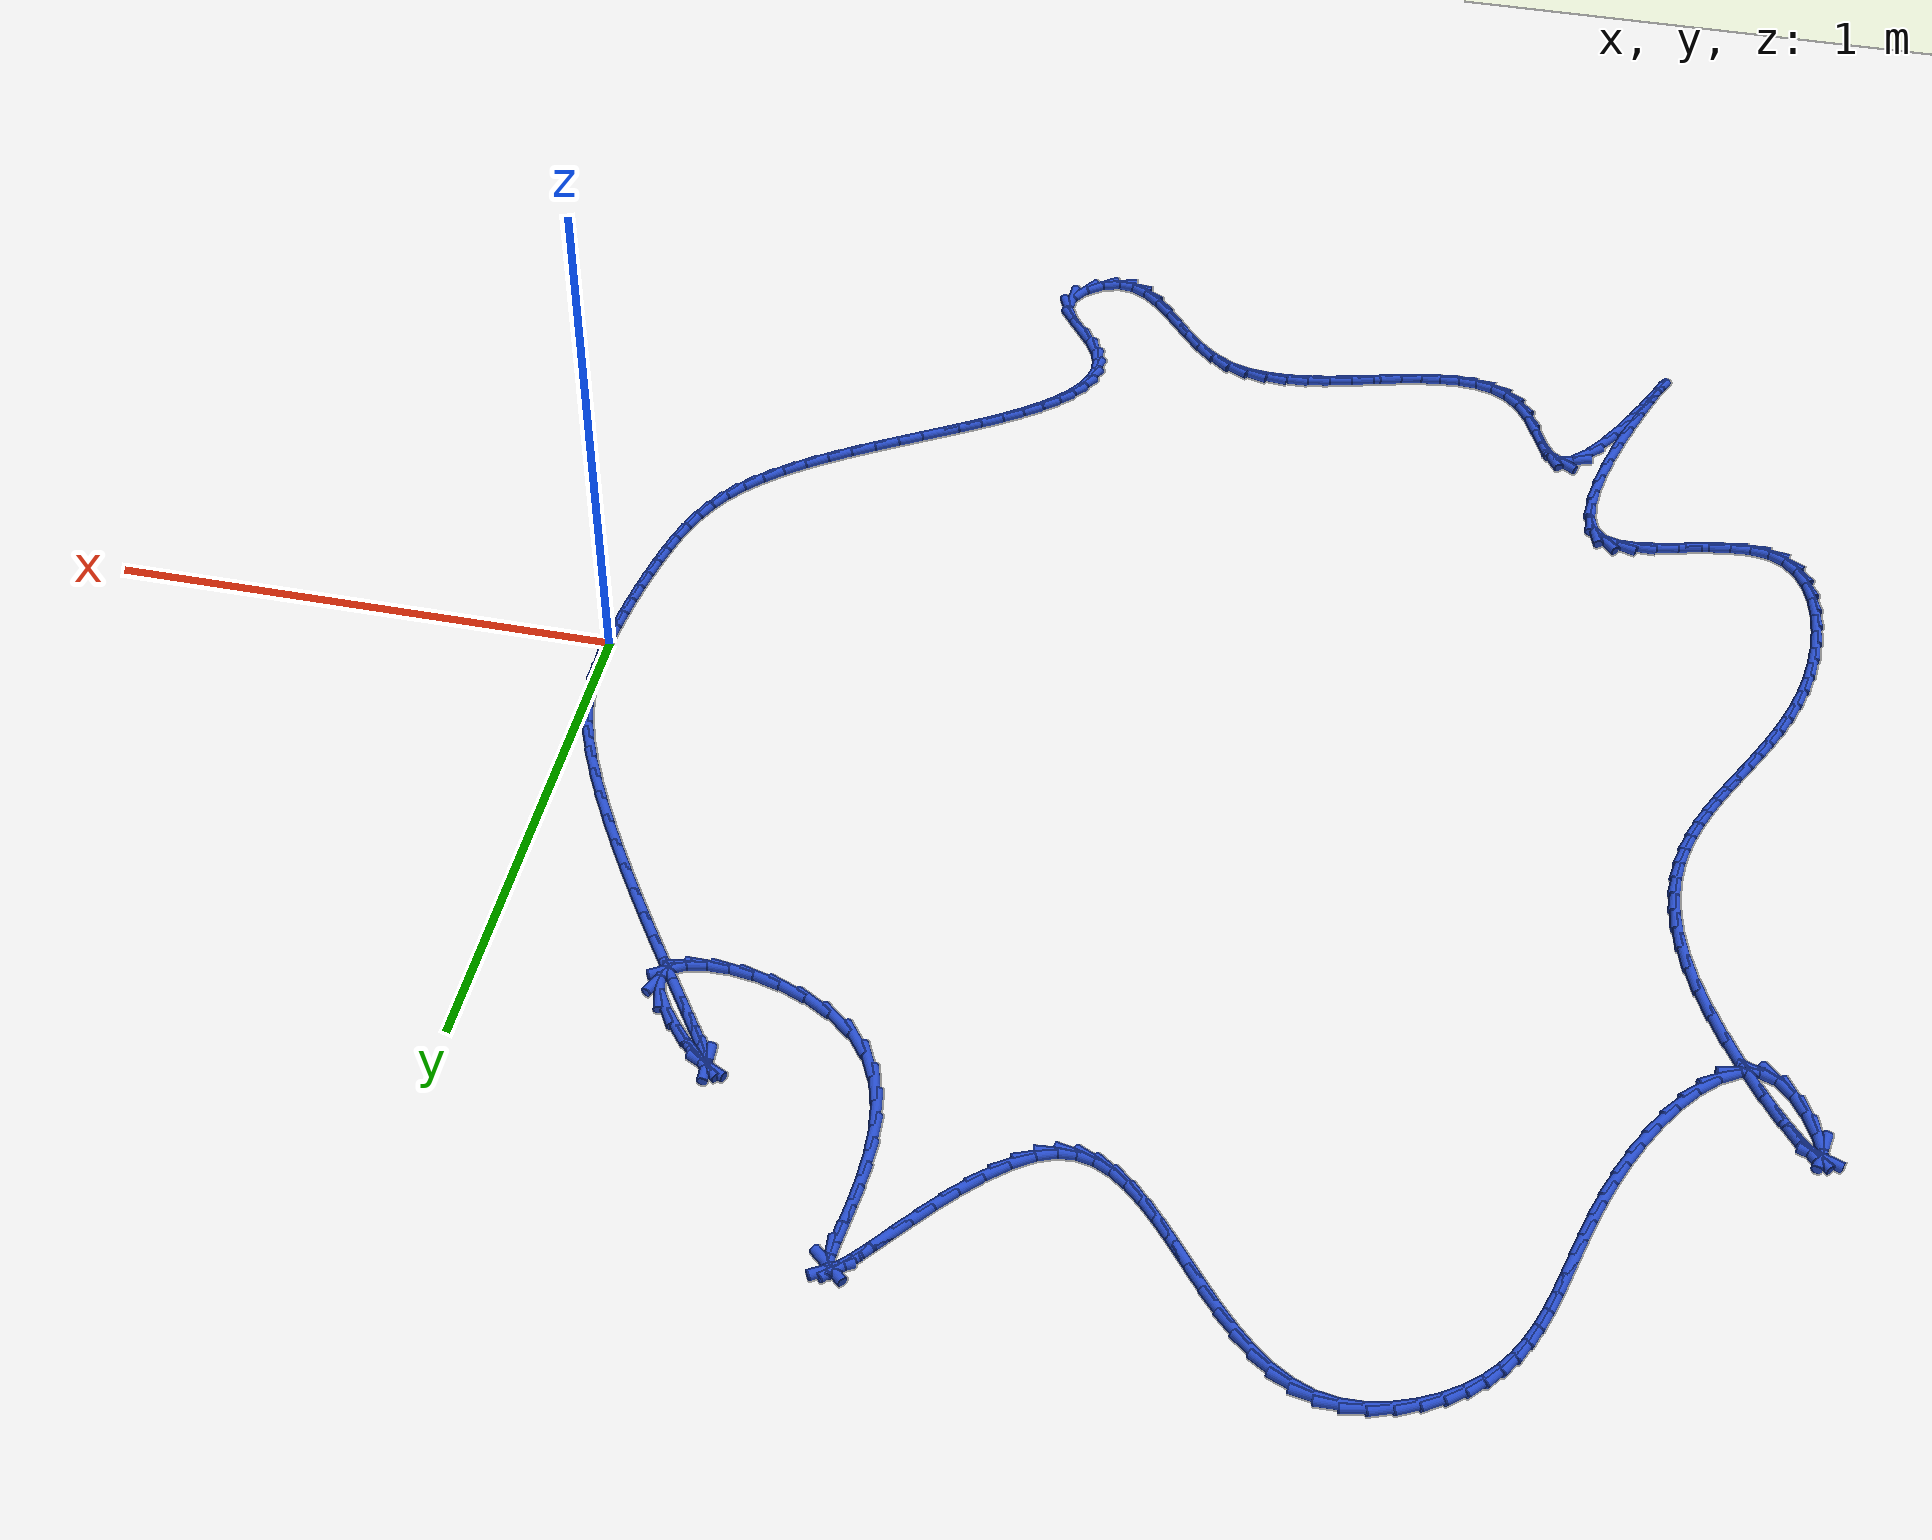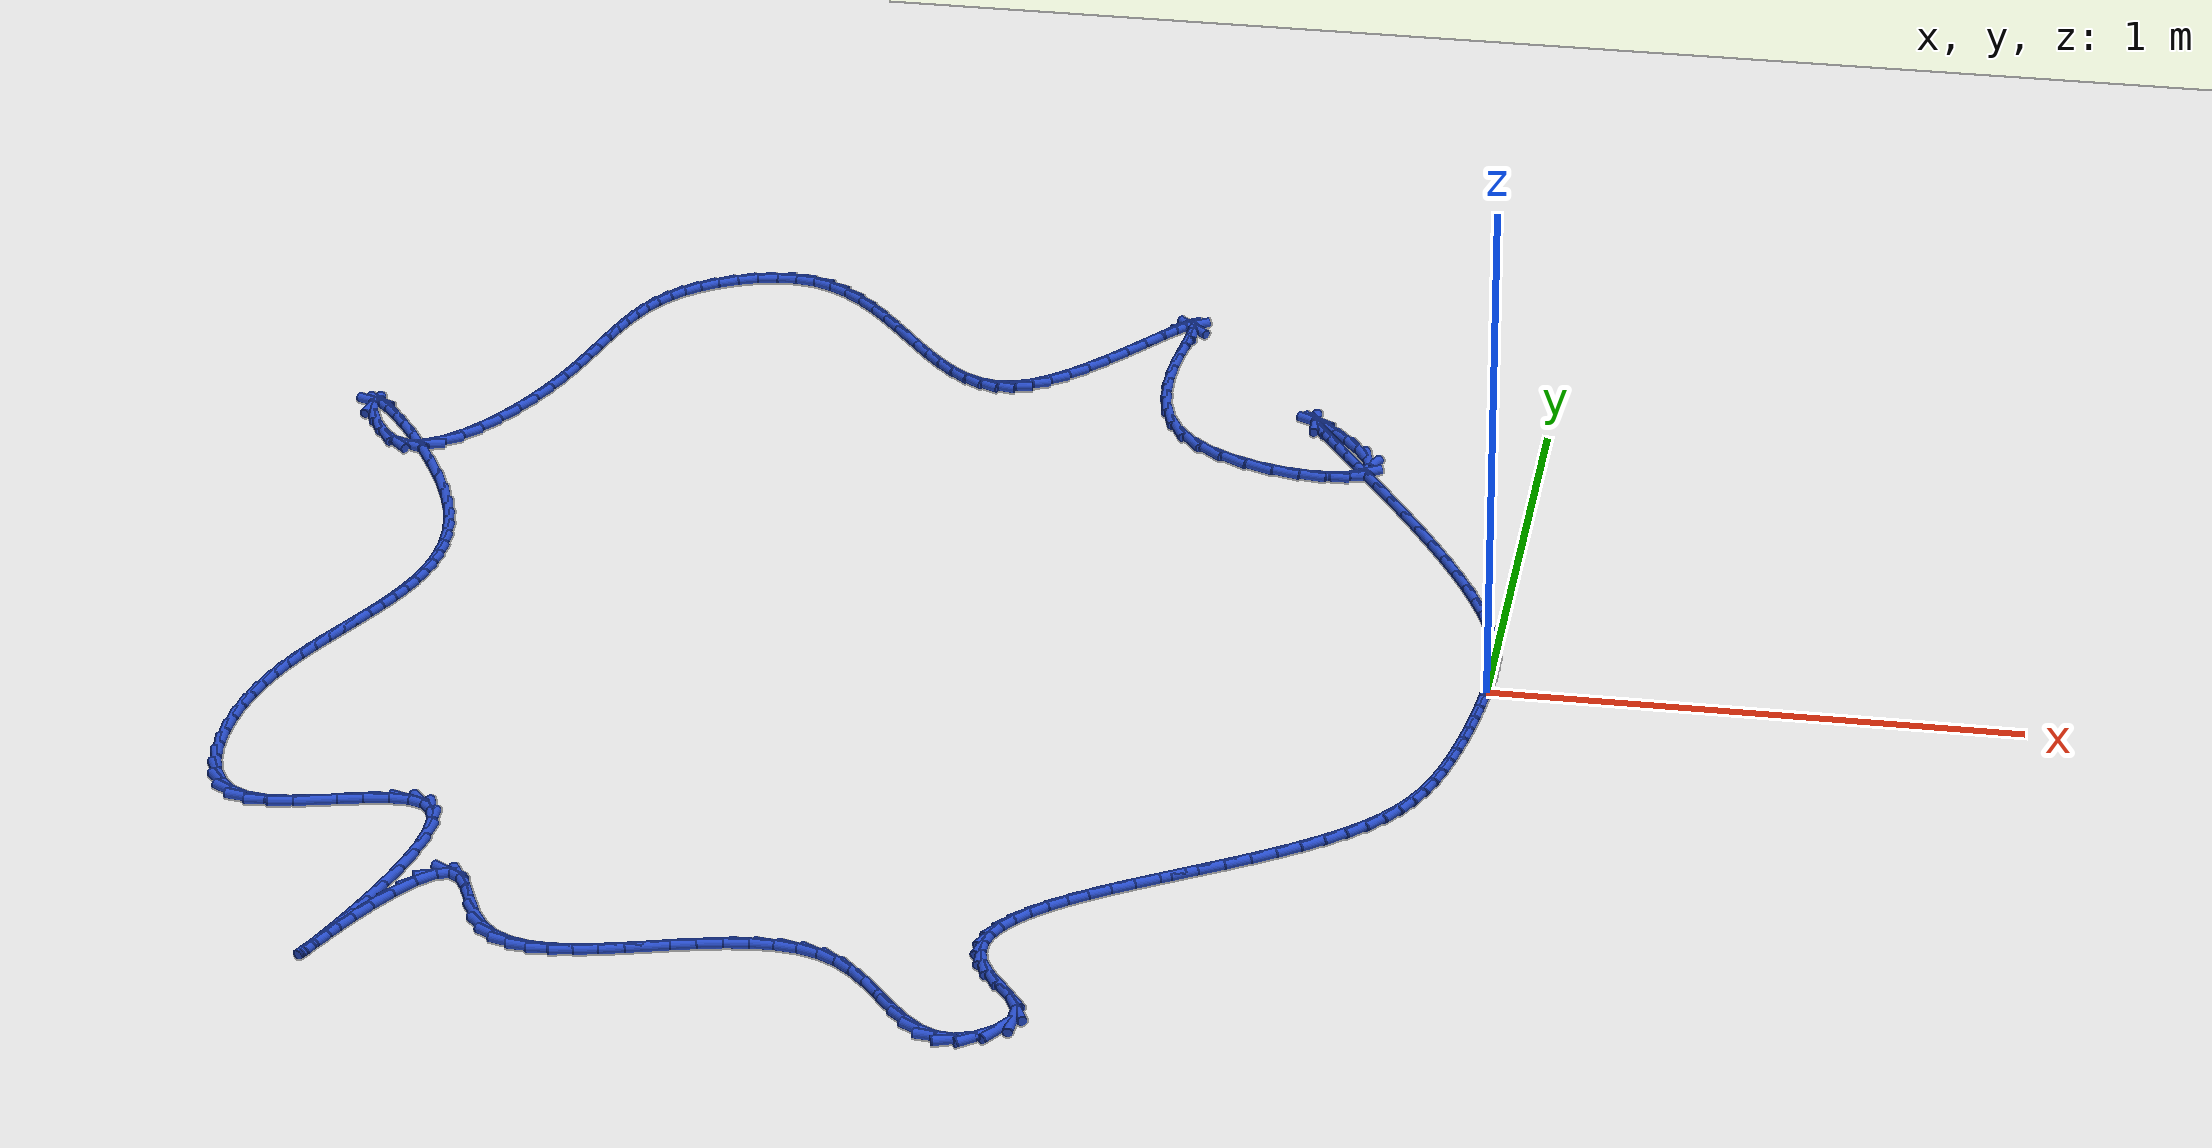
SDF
<sdf version="1.6">
 <world name="default">
  <light name="sun" type="directional">
   <pose>0 0 10 0 -0 0</pose>
   <diffuse>0.8 0.8 0.8 1</diffuse>
   <specular>0.2 0.2 0.2 1</specular>
   <attenuation>
    <range>1000</range>
    <constant>0.9</constant>
    <linear>0.01</linear>
    <quadratic>0.001</quadratic>
   </attenuation>
   <direction>-0.5 0.1 -0.9</direction>
  </light>
  <model name="ground_plane">
   <static>1</static>
   <link name="link">
    <collision name="collision">
     <geometry><plane><normal>0 0 1</normal><size>100 100</size></plane></geometry>
     <surface><friction><ode><mu>100</mu><mu2>50</mu2></ode></friction></surface>
    </collision>
    <visual name="visual">
     <cast_shadows>0</cast_shadows>
     <geometry><plane><normal>0 0 1</normal><size>100 100</size></plane></geometry>
     <material>
      <script><uri>file://media/materials/scripts/gazebo.material</uri><name>Gazebo/WhiteGlow</name></script>
     </material>
    </visual>
   </link>
  </model>
  <gravity>0 0 -9.8</gravity>
  <magnetic_field>6e-06 2.3e-05 -4.2e-05</magnetic_field>
  <atmosphere type="adiabatic"/>
  <physics name="default_physics" default="0" type="ode">
   <max_step_size>0.001</max_step_size>
   <real_time_factor>1</real_time_factor>
   <real_time_update_rate>1000</real_time_update_rate>
  </physics>
  <scene><ambient>0.4 0.4 0.4 1</ambient><background>0.7 0.7 0.7 1</background><shadows>1</shadows></scene>
  <spherical_coordinates>
   <surface_model>EARTH_WGS84</surface_model>
   <latitude_deg>0</latitude_deg>
   <longitude_deg>0</longitude_deg>
   <elevation>0</elevation>
   <heading_deg>0</heading_deg>
  </spherical_coordinates>
  <model name="line">
   <link name="link_0">
    <pose>4.0115480381963664e-18 0.0 0.01 0 1.57 1.5303201860089708</pose>
    <collision name="collision">
     <geometry><cylinder><radius>0.01</radius><length>0.08</length></cylinder></geometry>
    </collision>
    <visual name="visual">
     <material>
      <script><name>Gazebo/Blue</name><uri>file://media/materials/scripts/gazebo.material</uri></script>
     </material>
     <geometry><cylinder><radius>0.01</radius><length>0.08</length></cylinder></geometry>
    </visual>
   </link>
   <link name="link_1">
    <pose>0.001520172077840823 0.037536726144683 0.01 0 1.57 -1.569441561724418</pose>
    <collision name="collision">
     <geometry><cylinder><radius>0.01</radius><length>0.08</length></cylinder></geometry>
    </collision>
    <visual name="visual">
     <material>
      <script><name>Gazebo/Blue</name><uri>file://media/materials/scripts/gazebo.material</uri></script>
     </material>
     <geometry><cylinder><radius>0.01</radius><length>0.08</length></cylinder></geometry>
    </visual>
   </link>
   <link name="link_2">
    <pose>0.0014697098571924629 0.07478465264896869 0.01 0 1.57 -1.5113080191222836</pose>
    <collision name="collision">
     <geometry><cylinder><radius>0.01</radius><length>0.08</length></cylinder></geometry>
    </collision>
    <visual name="visual">
     <material>
      <script><name>Gazebo/Blue</name><uri>file://media/materials/scripts/gazebo.material</uri></script>
     </material>
     <geometry><cylinder><radius>0.01</radius><length>0.08</length></cylinder></geometry>
    </visual>
   </link>
   <link name="link_3">
    <pose>-0.0007749658739909663 0.11247318894364157 0.01 0 1.57 -1.4412465973038162</pose>
    <collision name="collision">
     <geometry><cylinder><radius>0.01</radius><length>0.08</length></cylinder></geometry>
    </collision>
    <visual name="visual">
     <material>
      <script><name>Gazebo/Blue</name><uri>file://media/materials/scripts/gazebo.material</uri></script>
     </material>
     <geometry><cylinder><radius>0.01</radius><length>0.08</length></cylinder></geometry>
    </visual>
   </link>
   <link name="link_4">
    <pose>-0.005837434327755361 0.15133174445948613 0.01 0 1.57 -1.3651048219305941</pose>
    <collision name="collision">
     <geometry><cylinder><radius>0.01</radius><length>0.08</length></cylinder></geometry>
    </collision>
    <visual name="visual">
     <material>
      <script><name>Gazebo/Blue</name><uri>file://media/materials/scripts/gazebo.material</uri></script>
     </material>
     <geometry><cylinder><radius>0.01</radius><length>0.08</length></cylinder></geometry>
    </visual>
   </link>
   <link name="link_5">
    <pose>-0.014341274716146612 0.1920897286272868 0.01 0 1.57 -1.2888235404271693</pose>
    <collision name="collision">
     <geometry><cylinder><radius>0.01</radius><length>0.08</length></cylinder></geometry>
    </collision>
    <visual name="visual">
     <material>
      <script><name>Gazebo/Blue</name><uri>file://media/materials/scripts/gazebo.material</uri></script>
     </material>
     <geometry><cylinder><radius>0.01</radius><length>0.08</length></cylinder></geometry>
    </visual>
   </link>
   <link name="link_6">
    <pose>-0.02691006625121061 0.23547655087782815 0.01 0 1.57 -1.2180053051059394</pose>
    <collision name="collision">
     <geometry><cylinder><radius>0.01</radius><length>0.08</length></cylinder></geometry>
    </collision>
    <visual name="visual">
     <material>
      <script><name>Gazebo/Blue</name><uri>file://media/materials/scripts/gazebo.material</uri></script>
     </material>
     <geometry><cylinder><radius>0.01</radius><length>0.08</length></cylinder></geometry>
    </visual>
   </link>
   <link name="link_7">
    <pose>-0.04409027080819526 0.28213720961980204 0.01 0 1.57 -1.1616342007853082</pose>
    <collision name="collision">
     <geometry><cylinder><radius>0.01</radius><length>0.08</length></cylinder></geometry>
    </collision>
    <visual name="visual">
     <material>
      <script><name>Gazebo/Blue</name><uri>file://media/materials/scripts/gazebo.material</uri></script>
     </material>
     <geometry><cylinder><radius>0.01</radius><length>0.08</length></cylinder></geometry>
    </visual>
   </link>
   <link name="link_8">
    <pose>-0.06565740063969394 0.3318728379479226 0.01 0 1.57 -1.1191465528507305</pose>
    <collision name="collision">
     <geometry><cylinder><radius>0.01</radius><length>0.08</length></cylinder></geometry>
    </collision>
    <visual name="visual">
     <material>
      <script><name>Gazebo/Blue</name><uri>file://media/materials/scripts/gazebo.material</uri></script>
     </material>
     <geometry><cylinder><radius>0.01</radius><length>0.08</length></cylinder></geometry>
    </visual>
   </link>
   <link name="link_9">
    <pose>-0.09094335428555372 0.383998998675797 0.01 0 1.57 -1.0862942908348723</pose>
    <collision name="collision">
     <geometry><cylinder><radius>0.01</radius><length>0.08</length></cylinder></geometry>
    </collision>
    <visual name="visual">
     <material>
      <script><name>Gazebo/Blue</name><uri>file://media/materials/scripts/gazebo.material</uri></script>
     </material>
     <geometry><cylinder><radius>0.01</radius><length>0.08</length></cylinder></geometry>
    </visual>
   </link>
   <link name="link_10">
    <pose>-0.11927471622429982 0.4378254379567816 0.01 0 1.57 -1.0603783241716511</pose>
    <collision name="collision">
     <geometry><cylinder><radius>0.01</radius><length>0.08</length></cylinder></geometry>
    </collision>
    <visual name="visual">
     <material>
      <script><name>Gazebo/Blue</name><uri>file://media/materials/scripts/gazebo.material</uri></script>
     </material>
     <geometry><cylinder><radius>0.01</radius><length>0.08</length></cylinder></geometry>
    </visual>
   </link>
   <link name="link_11">
    <pose>-0.1499780709344574 0.4926619019442317 0.01 0 1.57 -1.0396504630270211</pose>
    <collision name="collision">
     <geometry><cylinder><radius>0.01</radius><length>0.08</length></cylinder></geometry>
    </collision>
    <visual name="visual">
     <material>
      <script><name>Gazebo/Blue</name><uri>file://media/materials/scripts/gazebo.material</uri></script>
     </material>
     <geometry><cylinder><radius>0.01</radius><length>0.08</length></cylinder></geometry>
    </visual>
   </link>
   <link name="link_12">
    <pose>-0.18238000289455186 0.547818136791504 0.01 0 1.57 -1.0229527557633562</pose>
    <collision name="collision">
     <geometry><cylinder><radius>0.01</radius><length>0.08</length></cylinder></geometry>
    </collision>
    <visual name="visual">
     <material>
      <script><name>Gazebo/Blue</name><uri>file://media/materials/scripts/gazebo.material</uri></script>
     </material>
     <geometry><cylinder><radius>0.01</radius><length>0.08</length></cylinder></geometry>
    </visual>
   </link>
   <link name="link_13">
    <pose>-0.21580709658310823 0.6026038886519541 0.01 0 1.57 -1.009515108304731</pose>
    <collision name="collision">
     <geometry><cylinder><radius>0.01</radius><length>0.08</length></cylinder></geometry>
    </collision>
    <visual name="visual">
     <material>
      <script><name>Gazebo/Blue</name><uri>file://media/materials/scripts/gazebo.material</uri></script>
     </material>
     <geometry><cylinder><radius>0.01</radius><length>0.08</length></cylinder></geometry>
    </visual>
   </link>
   <link name="link_14">
    <pose>-0.24958593647865188 0.6563289036789381 0.01 0 1.57 -0.99884240137922</pose>
    <collision name="collision">
     <geometry><cylinder><radius>0.01</radius><length>0.08</length></cylinder></geometry>
    </collision>
    <visual name="visual">
     <material>
      <script><name>Gazebo/Blue</name><uri>file://media/materials/scripts/gazebo.material</uri></script>
     </material>
     <geometry><cylinder><radius>0.01</radius><length>0.08</length></cylinder></geometry>
    </visual>
   </link>
   <link name="link_15">
    <pose>-0.283043107059708 0.7083029280258119 0.01 0 1.57 -0.990658316889918</pose>
    <collision name="collision">
     <geometry><cylinder><radius>0.01</radius><length>0.08</length></cylinder></geometry>
    </collision>
    <visual name="visual">
     <material>
      <script><name>Gazebo/Blue</name><uri>file://media/materials/scripts/gazebo.material</uri></script>
     </material>
     <geometry><cylinder><radius>0.01</radius><length>0.08</length></cylinder></geometry>
    </visual>
   </link>
   <link name="link_16">
    <pose>-0.3155051928048018 0.7578357078459317 0.01 0 1.57 -0.9848944452828642</pose>
    <collision name="collision">
     <geometry><cylinder><radius>0.01</radius><length>0.08</length></cylinder></geometry>
    </collision>
    <visual name="visual">
     <material>
      <script><name>Gazebo/Blue</name><uri>file://media/materials/scripts/gazebo.material</uri></script>
     </material>
     <geometry><cylinder><radius>0.01</radius><length>0.08</length></cylinder></geometry>
    </visual>
   </link>
   <link name="link_17">
    <pose>-0.3462987781924587 0.8042369892926535 0.01 0 1.57 -0.9817324799922449</pose>
    <collision name="collision">
     <geometry><cylinder><radius>0.01</radius><length>0.08</length></cylinder></geometry>
    </collision>
    <visual name="visual">
     <material>
      <script><name>Gazebo/Blue</name><uri>file://media/materials/scripts/gazebo.material</uri></script>
     </material>
     <geometry><cylinder><radius>0.01</radius><length>0.08</length></cylinder></geometry>
    </visual>
   </link>
   <link name="link_18">
    <pose>-0.37475044770120364 0.8468165185193332 0.01 0 1.57 -0.9817398526930333</pose>
    <collision name="collision">
     <geometry><cylinder><radius>0.01</radius><length>0.08</length></cylinder></geometry>
    </collision>
    <visual name="visual">
     <material>
      <script><name>Gazebo/Blue</name><uri>file://media/materials/scripts/gazebo.material</uri></script>
     </material>
     <geometry><cylinder><radius>0.01</radius><length>0.08</length></cylinder></geometry>
    </visual>
   </link>
   <link name="link_19">
    <pose>-0.4001867858095618 0.8848840416793262 0.01 0 1.57 -0.98622639043805</pose>
    <collision name="collision">
     <geometry><cylinder><radius>0.01</radius><length>0.08</length></cylinder></geometry>
    </collision>
    <visual name="visual">
     <material>
      <script><name>Gazebo/Blue</name><uri>file://media/materials/scripts/gazebo.material</uri></script>
     </material>
     <geometry><cylinder><radius>0.01</radius><length>0.08</length></cylinder></geometry>
    </visual>
   </link>
   <link name="link_20">
    <pose>-0.42193437699605896 0.9177493049259897 0.01 0 1.57 -0.9982581880913247</pose>
    <collision name="collision">
     <geometry><cylinder><radius>0.01</radius><length>0.08</length></cylinder></geometry>
    </collision>
    <visual name="visual">
     <material>
      <script><name>Gazebo/Blue</name><uri>file://media/materials/scripts/gazebo.material</uri></script>
     </material>
     <geometry><cylinder><radius>0.01</radius><length>0.08</length></cylinder></geometry>
    </visual>
   </link>
   <link name="link_21">
    <pose>-0.4393198057392197 0.9447220544126789 0.01 0 1.57 -1.0262091492527965</pose>
    <collision name="collision">
     <geometry><cylinder><radius>0.01</radius><length>0.08</length></cylinder></geometry>
    </collision>
    <visual name="visual">
     <material>
      <script><name>Gazebo/Blue</name><uri>file://media/materials/scripts/gazebo.material</uri></script>
     </material>
     <geometry><cylinder><radius>0.01</radius><length>0.08</length></cylinder></geometry>
    </visual>
   </link>
   <link name="link_22">
    <pose>-0.4516696565175697 0.9651120362927501 0.01 0 1.57 -1.102137192627309</pose>
    <collision name="collision">
     <geometry><cylinder><radius>0.01</radius><length>0.08</length></cylinder></geometry>
    </collision>
    <visual name="visual">
     <material>
      <script><name>Gazebo/Blue</name><uri>file://media/materials/scripts/gazebo.material</uri></script>
     </material>
     <geometry><cylinder><radius>0.01</radius><length>0.08</length></cylinder></geometry>
    </visual>
   </link>
   <link name="link_23">
    <pose>-0.4583105138096338 0.9782289967195585 0.01 0 1.57 -1.5206900530026566</pose>
    <collision name="collision">
     <geometry><cylinder><radius>0.01</radius><length>0.08</length></cylinder></geometry>
    </collision>
    <visual name="visual">
     <material>
      <script><name>Gazebo/Blue</name><uri>file://media/materials/scripts/gazebo.material</uri></script>
     </material>
     <geometry><cylinder><radius>0.01</radius><length>0.08</length></cylinder></geometry>
    </visual>
   </link>
   <link name="link_24">
    <pose>-0.45856896209393766 0.9833826818464615 0.01 0 1.57 -0.4754818953234487</pose>
    <collision name="collision">
     <geometry><cylinder><radius>0.01</radius><length>0.08</length></cylinder></geometry>
    </collision>
    <visual name="visual">
     <material>
      <script><name>Gazebo/Blue</name><uri>file://media/materials/scripts/gazebo.material</uri></script>
     </material>
     <geometry><cylinder><radius>0.01</radius><length>0.08</length></cylinder></geometry>
    </visual>
   </link>
   <link name="link_25">
    <pose>-0.4517715858490064 0.9798828378268143 0.01 0 1.57 -0.7239857403627098</pose>
    <collision name="collision">
     <geometry><cylinder><radius>0.01</radius><length>0.08</length></cylinder></geometry>
    </collision>
    <visual name="visual">
     <material>
      <script><name>Gazebo/Blue</name><uri>file://media/materials/scripts/gazebo.material</uri></script>
     </material>
     <geometry><cylinder><radius>0.01</radius><length>0.08</length></cylinder></geometry>
    </visual>
   </link>
   <link name="link_26">
    <pose>-0.4372449695533649 0.9670392108139725 0.01 0 1.57 -0.7848509200731941</pose>
    <collision name="collision">
     <geometry><cylinder><radius>0.01</radius><length>0.08</length></cylinder></geometry>
    </collision>
    <visual name="visual">
     <material>
      <script><name>Gazebo/Blue</name><uri>file://media/materials/scripts/gazebo.material</uri></script>
     </material>
     <geometry><cylinder><radius>0.01</radius><length>0.08</length></cylinder></geometry>
    </visual>
   </link>
   <link name="link_27">
    <pose>-0.4144042268481272 0.9442234533261684 0.01 0 1.57 -0.8289464774994784</pose>
    <collision name="collision">
     <geometry><cylinder><radius>0.01</radius><length>0.08</length></cylinder></geometry>
    </collision>
    <visual name="visual">
     <material>
      <script><name>Gazebo/Blue</name><uri>file://media/materials/scripts/gazebo.material</uri></script>
     </material>
     <geometry><cylinder><radius>0.01</radius><length>0.08</length></cylinder></geometry>
    </visual>
   </link>
   <link name="link_28">
    <pose>-0.3857670296895338 0.9129767640683096 0.01 0 1.57 -0.9010110229813774</pose>
    <collision name="collision">
     <geometry><cylinder><radius>0.01</radius><length>0.08</length></cylinder></geometry>
    </collision>
    <visual name="visual">
     <material>
      <script><name>Gazebo/Blue</name><uri>file://media/materials/scripts/gazebo.material</uri></script>
     </material>
     <geometry><cylinder><radius>0.01</radius><length>0.08</length></cylinder></geometry>
    </visual>
   </link>
   <link name="link_29">
    <pose>-0.3576955420767075 0.8775287047683877 0.01 0 1.57 -1.0355459715413426</pose>
    <collision name="collision">
     <geometry><cylinder><radius>0.01</radius><length>0.08</length></cylinder></geometry>
    </collision>
    <visual name="visual">
     <material>
      <script><name>Gazebo/Blue</name><uri>file://media/materials/scripts/gazebo.material</uri></script>
     </material>
     <geometry><cylinder><radius>0.01</radius><length>0.08</length></cylinder></geometry>
    </visual>
   </link>
   <link name="link_30">
    <pose>-0.33679098569463717 0.8422760045814291 0.01 0 1.57 -1.3415357963832621</pose>
    <collision name="collision">
     <geometry><cylinder><radius>0.01</radius><length>0.08</length></cylinder></geometry>
    </collision>
    <visual name="visual">
     <material>
      <script><name>Gazebo/Blue</name><uri>file://media/materials/scripts/gazebo.material</uri></script>
     </material>
     <geometry><cylinder><radius>0.01</radius><length>0.08</length></cylinder></geometry>
    </visual>
   </link>
   <link name="link_31">
    <pose>-0.3296336503719831 0.8116056739503711 0.01 0 1.57 1.1548832909394582</pose>
    <collision name="collision">
     <geometry><cylinder><radius>0.01</radius><length>0.08</length></cylinder></geometry>
    </collision>
    <visual name="visual">
     <material>
      <script><name>Gazebo/Blue</name><uri>file://media/materials/scripts/gazebo.material</uri></script>
     </material>
     <geometry><cylinder><radius>0.01</radius><length>0.08</length></cylinder></geometry>
    </visual>
   </link>
   <link name="link_32">
    <pose>-0.3398286431576098 0.7885233386767022 0.01 0 1.57 0.5467809057627173</pose>
    <collision name="collision">
     <geometry><cylinder><radius>0.01</radius><length>0.08</length></cylinder></geometry>
    </collision>
    <visual name="visual">
     <material>
      <script><name>Gazebo/Blue</name><uri>file://media/materials/scripts/gazebo.material</uri></script>
     </material>
     <geometry><cylinder><radius>0.01</radius><length>0.08</length></cylinder></geometry>
    </visual>
   </link>
   <link name="link_33">
    <pose>-0.36494810593158183 0.7732335040784352 0.01 0 1.57 0.20402361852901116</pose>
    <collision name="collision">
     <geometry><cylinder><radius>0.01</radius><length>0.08</length></cylinder></geometry>
    </collision>
    <visual name="visual">
     <material>
      <script><name>Gazebo/Blue</name><uri>file://media/materials/scripts/gazebo.material</uri></script>
     </material>
     <geometry><cylinder><radius>0.01</radius><length>0.08</length></cylinder></geometry>
    </visual>
   </link>
   <link name="link_34">
    <pose>-0.40183410732965896 0.7656017006806173 0.01 0 1.57 0.002379215280133474</pose>
    <collision name="collision">
     <geometry><cylinder><radius>0.01</radius><length>0.08</length></cylinder></geometry>
    </collision>
    <visual name="visual">
     <material>
      <script><name>Gazebo/Blue</name><uri>file://media/materials/scripts/gazebo.material</uri></script>
     </material>
     <geometry><cylinder><radius>0.01</radius><length>0.08</length></cylinder></geometry>
    </visual>
   </link>
   <link name="link_35">
    <pose>-0.4473287159876009 0.7654934590082946 0.01 0 1.57 -0.14195385486934853</pose>
    <collision name="collision">
     <geometry><cylinder><radius>0.01</radius><length>0.08</length></cylinder></geometry>
    </collision>
    <visual name="visual">
     <material>
      <script><name>Gazebo/Blue</name><uri>file://media/materials/scripts/gazebo.material</uri></script>
     </material>
     <geometry><cylinder><radius>0.01</radius><length>0.08</length></cylinder></geometry>
    </visual>
   </link>
   <link name="link_36">
    <pose>-0.49827400054116744 0.7727743095865146 0.01 0 1.57 -0.26653194855929</pose>
    <collision name="collision">
     <geometry><cylinder><radius>0.01</radius><length>0.08</length></cylinder></geometry>
    </collision>
    <visual name="visual">
     <material>
      <script><name>Gazebo/Blue</name><uri>file://media/materials/scripts/gazebo.material</uri></script>
     </material>
     <geometry><cylinder><radius>0.01</radius><length>0.08</length></cylinder></geometry>
    </visual>
   </link>
   <link name="link_37">
    <pose>-0.5515120296261179 0.787309782940324 0.01 0 1.57 -0.39208100032786436</pose>
    <collision name="collision">
     <geometry><cylinder><radius>0.01</radius><length>0.08</length></cylinder></geometry>
    </collision>
    <visual name="visual">
     <material>
      <script><name>Gazebo/Blue</name><uri>file://media/materials/scripts/gazebo.material</uri></script>
     </material>
     <geometry><cylinder><radius>0.01</radius><length>0.08</length></cylinder></geometry>
    </visual>
   </link>
   <link name="link_38">
    <pose>-0.603884871878213 0.8089654095947705 0.01 0 1.57 -0.5347962024614153</pose>
    <collision name="collision">
     <geometry><cylinder><radius>0.01</radius><length>0.08</length></cylinder></geometry>
    </collision>
    <visual name="visual">
     <material>
      <script><name>Gazebo/Blue</name><uri>file://media/materials/scripts/gazebo.material</uri></script>
     </material>
     <geometry><cylinder><radius>0.01</radius><length>0.08</length></cylinder></geometry>
    </visual>
   </link>
   <link name="link_39">
    <pose>-0.6522345959332122 0.8376067200749006 0.01 0 1.57 -0.7114910100390018</pose>
    <collision name="collision">
     <geometry><cylinder><radius>0.01</radius><length>0.08</length></cylinder></geometry>
    </collision>
    <visual name="visual">
     <material>
      <script><name>Gazebo/Blue</name><uri>file://media/materials/scripts/gazebo.material</uri></script>
     </material>
     <geometry><cylinder><radius>0.01</radius><length>0.08</length></cylinder></geometry>
    </visual>
   </link>
   <link name="link_40">
    <pose>-0.6934032704268751 0.8730992449057611 0.01 0 1.57 -0.9291482017985081</pose>
    <collision name="collision">
     <geometry><cylinder><radius>0.01</radius><length>0.08</length></cylinder></geometry>
    </collision>
    <visual name="visual">
     <material>
      <script><name>Gazebo/Blue</name><uri>file://media/materials/scripts/gazebo.material</uri></script>
     </material>
     <geometry><cylinder><radius>0.01</radius><length>0.08</length></cylinder></geometry>
    </visual>
   </link>
   <link name="link_41">
    <pose>-0.7247947248926568 0.9151164952808559 0.01 0 1.57 -1.1340886970043256</pose>
    <collision name="collision">
     <geometry><cylinder><radius>0.01</radius><length>0.08</length></cylinder></geometry>
    </collision>
    <visual name="visual">
     <material>
      <script><name>Gazebo/Blue</name><uri>file://media/materials/scripts/gazebo.material</uri></script>
     </material>
     <geometry><cylinder><radius>0.01</radius><length>0.08</length></cylinder></geometry>
    </visual>
   </link>
   <link name="link_42">
    <pose>-0.7468201862753743 0.9623040033318098 0.01 0 1.57 -1.2998409286618695</pose>
    <collision name="collision">
     <geometry><cylinder><radius>0.01</radius><length>0.08</length></cylinder></geometry>
    </collision>
    <visual name="visual">
     <material>
      <script><name>Gazebo/Blue</name><uri>file://media/materials/scripts/gazebo.material</uri></script>
     </material>
     <geometry><cylinder><radius>0.01</radius><length>0.08</length></cylinder></geometry>
    </visual>
   </link>
   <link name="link_43">
    <pose>-0.7608930778095016 1.0129647336274197 0.01 0 1.57 -1.4280867984837846</pose>
    <collision name="collision">
     <geometry><cylinder><radius>0.01</radius><length>0.08</length></cylinder></geometry>
    </collision>
    <visual name="visual">
     <material>
      <script><name>Gazebo/Blue</name><uri>file://media/materials/scripts/gazebo.material</uri></script>
     </material>
     <geometry><cylinder><radius>0.01</radius><length>0.08</length></cylinder></geometry>
    </visual>
   </link>
   <link name="link_44">
    <pose>-0.7684275103307765 1.0654014157027956 0.01 0 1.57 -1.524935566924673</pose>
    <collision name="collision">
     <geometry><cylinder><radius>0.01</radius><length>0.08</length></cylinder></geometry>
    </collision>
    <visual name="visual">
     <material>
      <script><name>Gazebo/Blue</name><uri>file://media/materials/scripts/gazebo.material</uri></script>
     </material>
     <geometry><cylinder><radius>0.01</radius><length>0.08</length></cylinder></geometry>
    </visual>
   </link>
   <link name="link_45">
    <pose>-0.7708375946749381 1.1179167790930475 0.01 0 1.57 1.545256981210594</pose>
    <collision name="collision">
     <geometry><cylinder><radius>0.01</radius><length>0.08</length></cylinder></geometry>
    </collision>
    <visual name="visual">
     <material>
      <script><name>Gazebo/Blue</name><uri>file://media/materials/scripts/gazebo.material</uri></script>
     </material>
     <geometry><cylinder><radius>0.01</radius><length>0.08</length></cylinder></geometry>
    </visual>
   </link>
   <link name="link_46">
    <pose>-0.7695374416777249 1.168813553333286 0.01 0 1.57 1.4953573665496562</pose>
    <collision name="collision">
     <geometry><cylinder><radius>0.01</radius><length>0.08</length></cylinder></geometry>
    </collision>
    <visual name="visual">
     <material>
      <script><name>Gazebo/Blue</name><uri>file://media/materials/scripts/gazebo.material</uri></script>
     </material>
     <geometry><cylinder><radius>0.01</radius><length>0.08</length></cylinder></geometry>
    </visual>
   </link>
   <link name="link_47">
    <pose>-0.7659411621748754 1.2163944679586205 0.01 0 1.57 1.4659780381797278</pose>
    <collision name="collision">
     <geometry><cylinder><radius>0.01</radius><length>0.08</length></cylinder></geometry>
    </collision>
    <visual name="visual">
     <material>
      <script><name>Gazebo/Blue</name><uri>file://media/materials/scripts/gazebo.material</uri></script>
     </material>
     <geometry><cylinder><radius>0.01</radius><length>0.08</length></cylinder></geometry>
    </visual>
   </link>
   <link name="link_48">
    <pose>-0.761462867002128 1.2589622525041617 0.01 0 1.57 1.4611847831966518</pose>
    <collision name="collision">
     <geometry><cylinder><radius>0.01</radius><length>0.08</length></cylinder></geometry>
    </collision>
    <visual name="visual">
     <material>
      <script><name>Gazebo/Blue</name><uri>file://media/materials/scripts/gazebo.material</uri></script>
     </material>
     <geometry><cylinder><radius>0.01</radius><length>0.08</length></cylinder></geometry>
    </visual>
   </link>
   <link name="link_49">
    <pose>-0.7575166669952214 1.2948196365050189 0.01 0 1.57 1.498064558507656</pose>
    <collision name="collision">
     <geometry><cylinder><radius>0.01</radius><length>0.08</length></cylinder></geometry>
    </collision>
    <visual name="visual">
     <material>
      <script><name>Gazebo/Blue</name><uri>file://media/materials/scripts/gazebo.material</uri></script>
     </material>
     <geometry><cylinder><radius>0.01</radius><length>0.08</length></cylinder></geometry>
    </visual>
   </link>
   <link name="link_50">
    <pose>-0.7555166729898943 1.3222693494963025 0.01 0 1.57 -1.4925281318502241</pose>
    <collision name="collision">
     <geometry><cylinder><radius>0.01</radius><length>0.08</length></cylinder></geometry>
    </collision>
    <visual name="visual">
     <material>
      <script><name>Gazebo/Blue</name><uri>file://media/materials/scripts/gazebo.material</uri></script>
     </material>
     <geometry><cylinder><radius>0.01</radius><length>0.08</length></cylinder></geometry>
    </visual>
   </link>
   <link name="link_51">
    <pose>-0.7568769958218851 1.3396141210131227 0.01 0 1.57 -0.7347325765236543</pose>
    <collision name="collision">
     <geometry><cylinder><radius>0.01</radius><length>0.08</length></cylinder></geometry>
    </collision>
    <visual name="visual">
     <material>
      <script><name>Gazebo/Blue</name><uri>file://media/materials/scripts/gazebo.material</uri></script>
     </material>
     <geometry><cylinder><radius>0.01</radius><length>0.08</length></cylinder></geometry>
    </visual>
   </link>
   <link name="link_52">
    <pose>-0.7630117305097015 1.3451567104547892 0.01 0 1.57 0.5439264333364534</pose>
    <collision name="collision">
     <geometry><cylinder><radius>0.01</radius><length>0.08</length></cylinder></geometry>
    </collision>
    <visual name="visual">
     <material>
      <script><name>Gazebo/Blue</name><uri>file://media/materials/scripts/gazebo.material</uri></script>
     </material>
     <geometry><cylinder><radius>0.01</radius><length>0.08</length></cylinder></geometry>
    </visual>
   </link>
   <link name="link_53">
    <pose>-0.7749422431518169 1.337941380919843 0.01 0 1.57 0.8114322425674704</pose>
    <collision name="collision">
     <geometry><cylinder><radius>0.01</radius><length>0.08</length></cylinder></geometry>
    </collision>
    <visual name="visual">
     <material>
      <script><name>Gazebo/Blue</name><uri>file://media/materials/scripts/gazebo.material</uri></script>
     </material>
     <geometry><cylinder><radius>0.01</radius><length>0.08</length></cylinder></geometry>
    </visual>
   </link>
   <link name="link_54">
    <pose>-0.7922774429933019 1.3196792273299247 0.01 0 1.57 0.8863629968806034</pose>
    <collision name="collision">
     <geometry><cylinder><radius>0.01</radius><length>0.08</length></cylinder></geometry>
    </collision>
    <visual name="visual">
     <material>
      <script><name>Gazebo/Blue</name><uri>file://media/materials/scripts/gazebo.material</uri></script>
     </material>
     <geometry><cylinder><radius>0.01</radius><length>0.08</length></cylinder></geometry>
    </visual>
   </link>
   <link name="link_55">
    <pose>-0.8143088159136778 1.2926806653792762 0.01 0 1.57 0.9093402728886115</pose>
    <collision name="collision">
     <geometry><cylinder><radius>0.01</radius><length>0.08</length></cylinder></geometry>
    </collision>
    <visual name="visual">
     <material>
      <script><name>Gazebo/Blue</name><uri>file://media/materials/scripts/gazebo.material</uri></script>
     </material>
     <geometry><cylinder><radius>0.01</radius><length>0.08</length></cylinder></geometry>
    </visual>
   </link>
   <link name="link_56">
    <pose>-0.8403278477924655 1.2592561107621378 0.01 0 1.57 0.908090627107653</pose>
    <collision name="collision">
     <geometry><cylinder><radius>0.01</radius><length>0.08</length></cylinder></geometry>
    </collision>
    <visual name="visual">
     <material>
      <script><name>Gazebo/Blue</name><uri>file://media/materials/scripts/gazebo.material</uri></script>
     </material>
     <geometry><cylinder><radius>0.01</radius><length>0.08</length></cylinder></geometry>
    </visual>
   </link>
   <link name="link_57">
    <pose>-0.869626024509186 1.2217159791727499 0.01 0 1.57 0.8900010000514996</pose>
    <collision name="collision">
     <geometry><cylinder><radius>0.01</radius><length>0.08</length></cylinder></geometry>
    </collision>
    <visual name="visual">
     <material>
      <script><name>Gazebo/Blue</name><uri>file://media/materials/scripts/gazebo.material</uri></script>
     </material>
     <geometry><cylinder><radius>0.01</radius><length>0.08</length></cylinder></geometry>
    </visual>
   </link>
   <link name="link_58">
    <pose>-0.9014948319433603 1.1823706863053538 0.01 0 1.57 0.8556838305200329</pose>
    <collision name="collision">
     <geometry><cylinder><radius>0.01</radius><length>0.08</length></cylinder></geometry>
    </collision>
    <visual name="visual">
     <material>
      <script><name>Gazebo/Blue</name><uri>file://media/materials/scripts/gazebo.material</uri></script>
     </material>
     <geometry><cylinder><radius>0.01</radius><length>0.08</length></cylinder></geometry>
    </visual>
   </link>
   <link name="link_59">
    <pose>-0.9352257559745096 1.1435306478541902 0.01 0 1.57 0.801471516019866</pose>
    <collision name="collision">
     <geometry><cylinder><radius>0.01</radius><length>0.08</length></cylinder></geometry>
    </collision>
    <visual name="visual">
     <material>
      <script><name>Gazebo/Blue</name><uri>file://media/materials/scripts/gazebo.material</uri></script>
     </material>
     <geometry><cylinder><radius>0.01</radius><length>0.08</length></cylinder></geometry>
    </visual>
   </link>
   <link name="link_60">
    <pose>-0.9701102824821544 1.1075062795135 0.01 0 1.57 0.718587390450852</pose>
    <collision name="collision">
     <geometry><cylinder><radius>0.01</radius><length>0.08</length></cylinder></geometry>
    </collision>
    <visual name="visual">
     <material>
      <script><name>Gazebo/Blue</name><uri>file://media/materials/scripts/gazebo.material</uri></script>
     </material>
     <geometry><cylinder><radius>0.01</radius><length>0.08</length></cylinder></geometry>
    </visual>
   </link>
   <link name="link_61">
    <pose>-1.005439897345817 1.0766079969775242 0.01 0 1.57 0.5896655087444514</pose>
    <collision name="collision">
     <geometry><cylinder><radius>0.01</radius><length>0.08</length></cylinder></geometry>
    </collision>
    <visual name="visual">
     <material>
      <script><name>Gazebo/Blue</name><uri>file://media/materials/scripts/gazebo.material</uri></script>
     </material>
     <geometry><cylinder><radius>0.01</radius><length>0.08</length></cylinder></geometry>
    </visual>
   </link>
   <link name="link_62">
    <pose>-1.0405060864450175 1.0531462159405025 0.01 0 1.57 0.3829518375990623</pose>
    <collision name="collision">
     <geometry><cylinder><radius>0.01</radius><length>0.08</length></cylinder></geometry>
    </collision>
    <visual name="visual">
     <material>
      <script><name>Gazebo/Blue</name><uri>file://media/materials/scripts/gazebo.material</uri></script>
     </material>
     <geometry><cylinder><radius>0.01</radius><length>0.08</length></cylinder></geometry>
    </visual>
   </link>
   <link name="link_63">
    <pose>-1.0746060353433733 1.0394094089830614 0.01 0 1.57 0.09279475281359069</pose>
    <collision name="collision">
     <geometry><cylinder><radius>0.01</radius><length>0.08</length></cylinder></geometry>
    </collision>
    <visual name="visual">
     <material>
      <script><name>Gazebo/Blue</name><uri>file://media/materials/scripts/gazebo.material</uri></script>
     </material>
     <geometry><cylinder><radius>0.01</radius><length>0.08</length></cylinder></geometry>
    </visual>
   </link>
   <link name="link_64">
    <pose>-1.1073815626005357 1.0363592521723168 0.01 0 1.57 -0.20377198745137173</pose>
    <collision name="collision">
     <geometry><cylinder><radius>0.01</radius><length>0.08</length></cylinder></geometry>
    </collision>
    <visual name="visual">
     <material>
      <script><name>Gazebo/Blue</name><uri>file://media/materials/scripts/gazebo.material</uri></script>
     </material>
     <geometry><cylinder><radius>0.01</radius><length>0.08</length></cylinder></geometry>
    </visual>
   </link>
   <link name="link_65">
    <pose>-1.139010198397188 1.0428949948222401 0.01 0 1.57 -0.45027254967111524</pose>
    <collision name="collision">
     <geometry><cylinder><radius>0.01</radius><length>0.08</length></cylinder></geometry>
    </collision>
    <visual name="visual">
     <material>
      <script><name>Gazebo/Blue</name><uri>file://media/materials/scripts/gazebo.material</uri></script>
     </material>
     <geometry><cylinder><radius>0.01</radius><length>0.08</length></cylinder></geometry>
    </visual>
   </link>
   <link name="link_66">
    <pose>-1.1697157349771072 1.057737782743294 0.01 0 1.57 -0.629847561179597</pose>
    <collision name="collision">
     <geometry><cylinder><radius>0.01</radius><length>0.08</length></cylinder></geometry>
    </collision>
    <visual name="visual">
     <material>
      <script><name>Gazebo/Blue</name><uri>file://media/materials/scripts/gazebo.material</uri></script>
     </material>
     <geometry><cylinder><radius>0.01</radius><length>0.08</length></cylinder></geometry>
    </visual>
   </link>
   <link name="link_67">
    <pose>-1.199721964584069 1.0796087617459413 0.01 0 1.57 -0.7519834045007319</pose>
    <collision name="collision">
     <geometry><cylinder><radius>0.01</radius><length>0.08</length></cylinder></geometry>
    </collision>
    <visual name="visual">
     <material>
      <script><name>Gazebo/Blue</name><uri>file://media/materials/scripts/gazebo.material</uri></script>
     </material>
     <geometry><cylinder><radius>0.01</radius><length>0.08</length></cylinder></geometry>
    </visual>
   </link>
   <link name="link_68">
    <pose>-1.2292526794618501 1.1072290776406442 0.01 0 1.57 -0.8311835748317734</pose>
    <collision name="collision">
     <geometry><cylinder><radius>0.01</radius><length>0.08</length></cylinder></geometry>
    </collision>
    <visual name="visual">
     <material>
      <script><name>Gazebo/Blue</name><uri>file://media/materials/scripts/gazebo.material</uri></script>
     </material>
     <geometry><cylinder><radius>0.01</radius><length>0.08</length></cylinder></geometry>
    </visual>
   </link>
   <link name="link_69">
    <pose>-1.2585316718542263 1.139319876237865 0.01 0 1.57 -0.8785884627608861</pose>
    <collision name="collision">
     <geometry><cylinder><radius>0.01</radius><length>0.08</length></cylinder></geometry>
    </collision>
    <visual name="visual">
     <material>
      <script><name>Gazebo/Blue</name><uri>file://media/materials/scripts/gazebo.material</uri></script>
     </material>
     <geometry><cylinder><radius>0.01</radius><length>0.08</length></cylinder></geometry>
    </visual>
   </link>
   <link name="link_70">
    <pose>-1.2877827340049741 1.1746023033480661 0.01 0 1.57 -0.901145431860354</pose>
    <collision name="collision">
     <geometry><cylinder><radius>0.01</radius><length>0.08</length></cylinder></geometry>
    </collision>
    <visual name="visual">
     <material>
      <script><name>Gazebo/Blue</name><uri>file://media/materials/scripts/gazebo.material</uri></script>
     </material>
     <geometry><cylinder><radius>0.01</radius><length>0.08</length></cylinder></geometry>
    </visual>
   </link>
   <link name="link_71">
    <pose>-1.3172296581578695 1.2117975047817104 0.01 0 1.57 -0.9024827673888898</pose>
    <collision name="collision">
     <geometry><cylinder><radius>0.01</radius><length>0.08</length></cylinder></geometry>
    </collision>
    <visual name="visual">
     <material>
      <script><name>Gazebo/Blue</name><uri>file://media/materials/scripts/gazebo.material</uri></script>
     </material>
     <geometry><cylinder><radius>0.01</radius><length>0.08</length></cylinder></geometry>
    </visual>
   </link>
   <link name="link_72">
    <pose>-1.347096236556689 1.2496266263492606 0.01 0 1.57 -0.8836733652518334</pose>
    <collision name="collision">
     <geometry><cylinder><radius>0.01</radius><length>0.08</length></cylinder></geometry>
    </collision>
    <visual name="visual">
     <material>
      <script><name>Gazebo/Blue</name><uri>file://media/materials/scripts/gazebo.material</uri></script>
     </material>
     <geometry><cylinder><radius>0.01</radius><length>0.08</length></cylinder></geometry>
    </visual>
   </link>
   <link name="link_73">
    <pose>-1.3776062614452085 1.2868108138611778 0.01 0 1.57 -0.8436047259654775</pose>
    <collision name="collision">
     <geometry><cylinder><radius>0.01</radius><length>0.08</length></cylinder></geometry>
    </collision>
    <visual name="visual">
     <material>
      <script><name>Gazebo/Blue</name><uri>file://media/materials/scripts/gazebo.material</uri></script>
     </material>
     <geometry><cylinder><radius>0.01</radius><length>0.08</length></cylinder></geometry>
    </visual>
   </link>
   <link name="link_74">
    <pose>-1.4089835250672047 1.3220712131279255 0.01 0 1.57 -0.7790358923647409</pose>
    <collision name="collision">
     <geometry><cylinder><radius>0.01</radius><length>0.08</length></cylinder></geometry>
    </collision>
    <visual name="visual">
     <material>
      <script><name>Gazebo/Blue</name><uri>file://media/materials/scripts/gazebo.material</uri></script>
     </material>
     <geometry><cylinder><radius>0.01</radius><length>0.08</length></cylinder></geometry>
    </visual>
   </link>
   <link name="link_75">
    <pose>-1.4414518196664534 1.3541289699599663 0.01 0 1.57 -0.6845852755766088</pose>
    <collision name="collision">
     <geometry><cylinder><radius>0.01</radius><length>0.08</length></cylinder></geometry>
    </collision>
    <visual name="visual">
     <material>
      <script><name>Gazebo/Blue</name><uri>file://media/materials/scripts/gazebo.material</uri></script>
     </material>
     <geometry><cylinder><radius>0.01</radius><length>0.08</length></cylinder></geometry>
    </visual>
   </link>
   <link name="link_76">
    <pose>-1.475234937486732 1.3817052301677628 0.01 0 1.57 -0.5532849950577404</pose>
    <collision name="collision">
     <geometry><cylinder><radius>0.01</radius><length>0.08</length></cylinder></geometry>
    </collision>
    <visual name="visual">
     <material>
      <script><name>Gazebo/Blue</name><uri>file://media/materials/scripts/gazebo.material</uri></script>
     </material>
     <geometry><cylinder><radius>0.01</radius><length>0.08</length></cylinder></geometry>
    </visual>
   </link>
   <link name="link_77">
    <pose>-1.5105566707718152 1.4035211395617768 0.01 0 1.57 -0.3791817531269696</pose>
    <collision name="collision">
     <geometry><cylinder><radius>0.01</radius><length>0.08</length></cylinder></geometry>
    </collision>
    <visual name="visual">
     <material>
      <script><name>Gazebo/Blue</name><uri>file://media/materials/scripts/gazebo.material</uri></script>
     </material>
     <geometry><cylinder><radius>0.01</radius><length>0.08</length></cylinder></geometry>
    </visual>
   </link>
   <link name="link_78">
    <pose>-1.54764081176548 1.4182978439524705 0.01 0 1.57 -0.1655571798216257</pose>
    <collision name="collision">
     <geometry><cylinder><radius>0.01</radius><length>0.08</length></cylinder></geometry>
    </collision>
    <visual name="visual">
     <material>
      <script><name>Gazebo/Blue</name><uri>file://media/materials/scripts/gazebo.material</uri></script>
     </material>
     <geometry><cylinder><radius>0.01</radius><length>0.08</length></cylinder></geometry>
    </visual>
   </link>
   <link name="link_79">
    <pose>-1.5866728506023555 1.4248195724649755 0.01 0 1.57 0.041620329727861935</pose>
    <collision name="collision">
     <geometry><cylinder><radius>0.01</radius><length>0.08</length></cylinder></geometry>
    </collision>
    <visual name="visual">
     <material>
      <script><name>Gazebo/Blue</name><uri>file://media/materials/scripts/gazebo.material</uri></script>
     </material>
     <geometry><cylinder><radius>0.01</radius><length>0.08</length></cylinder></geometry>
    </visual>
   </link>
   <link name="link_80">
    <pose>-1.6270691551093681 1.4231372934624404 0.01 0 1.57 0.21090526527328898</pose>
    <collision name="collision">
     <geometry><cylinder><radius>0.01</radius><length>0.08</length></cylinder></geometry>
    </collision>
    <visual name="visual">
     <material>
      <script><name>Gazebo/Blue</name><uri>file://media/materials/scripts/gazebo.material</uri></script>
     </material>
     <geometry><cylinder><radius>0.01</radius><length>0.08</length></cylinder></geometry>
    </visual>
   </link>
   <link name="link_81">
    <pose>-1.6675344001051189 1.4144741288784382 0.01 0 1.57 0.35142322046466395</pose>
    <collision name="collision">
     <geometry><cylinder><radius>0.01</radius><length>0.08</length></cylinder></geometry>
    </collision>
    <visual name="visual">
     <material>
      <script><name>Gazebo/Blue</name><uri>file://media/materials/scripts/gazebo.material</uri></script>
     </material>
     <geometry><cylinder><radius>0.01</radius><length>0.08</length></cylinder></geometry>
    </visual>
   </link>
   <link name="link_82">
    <pose>-1.7067464658470601 1.4000973311075005 0.01 0 1.57 0.4746094546529808</pose>
    <collision name="collision">
     <geometry><cylinder><radius>0.01</radius><length>0.08</length></cylinder></geometry>
    </collision>
    <visual name="visual">
     <material>
      <script><name>Gazebo/Blue</name><uri>file://media/materials/scripts/gazebo.material</uri></script>
     </material>
     <geometry><cylinder><radius>0.01</radius><length>0.08</length></cylinder></geometry>
    </visual>
   </link>
   <link name="link_83">
    <pose>-1.7433832325926457 1.3812741525441619 0.01 0 1.57 0.5917147439178143</pose>
    <collision name="collision">
     <geometry><cylinder><radius>0.01</radius><length>0.08</length></cylinder></geometry>
    </collision>
    <visual name="visual">
     <material>
      <script><name>Gazebo/Blue</name><uri>file://media/materials/scripts/gazebo.material</uri></script>
     </material>
     <geometry><cylinder><radius>0.01</radius><length>0.08</length></cylinder></geometry>
    </visual>
   </link>
   <link name="link_84">
    <pose>-1.7761245141381952 1.3592706370469525 0.01 0 1.57 0.7127917252627441</pose>
    <collision name="collision">
     <geometry><cylinder><radius>0.01</radius><length>0.08</length></cylinder></geometry>
    </collision>
    <visual name="visual">
     <material>
      <script><name>Gazebo/Blue</name><uri>file://media/materials/scripts/gazebo.material</uri></script>
     </material>
     <geometry><cylinder><radius>0.01</radius><length>0.08</length></cylinder></geometry>
    </visual>
   </link>
   <link name="link_85">
    <pose>-1.8041716083683887 1.3350268809052623 0.01 0 1.57 0.8358842722831661</pose>
    <collision name="collision">
     <geometry><cylinder><radius>0.01</radius><length>0.08</length></cylinder></geometry>
    </collision>
    <visual name="visual">
     <material>
      <script><name>Gazebo/Blue</name><uri>file://media/materials/scripts/gazebo.material</uri></script>
     </material>
     <geometry><cylinder><radius>0.01</radius><length>0.08</length></cylinder></geometry>
    </visual>
   </link>
   <link name="link_86">
    <pose>-1.8279495651309479 1.3087180884654763 0.01 0 1.57 0.953146820202422</pose>
    <collision name="collision">
     <geometry><cylinder><radius>0.01</radius><length>0.08</length></cylinder></geometry>
    </collision>
    <visual name="visual">
     <material>
      <script><name>Gazebo/Blue</name><uri>file://media/materials/scripts/gazebo.material</uri></script>
     </material>
     <geometry><cylinder><radius>0.01</radius><length>0.08</length></cylinder></geometry>
    </visual>
   </link>
   <link name="link_87">
    <pose>-1.8480587753543565 1.2804098691691266 0.01 0 1.57 1.0576609260138956</pose>
    <collision name="collision">
     <geometry><cylinder><radius>0.01</radius><length>0.08</length></cylinder></geometry>
    </collision>
    <visual name="visual">
     <material>
      <script><name>Gazebo/Blue</name><uri>file://media/materials/scripts/gazebo.material</uri></script>
     </material>
     <geometry><cylinder><radius>0.01</radius><length>0.08</length></cylinder></geometry>
    </visual>
   </link>
   <link name="link_88">
    <pose>-1.8650996299671 1.2501678324577463 0.01 0 1.57 1.1447542538550988</pose>
    <collision name="collision">
     <geometry><cylinder><radius>0.01</radius><length>0.08</length></cylinder></geometry>
    </collision>
    <visual name="visual">
     <material>
      <script><name>Gazebo/Blue</name><uri>file://media/materials/scripts/gazebo.material</uri></script>
     </material>
     <geometry><cylinder><radius>0.01</radius><length>0.08</length></cylinder></geometry>
    </visual>
   </link>
   <link name="link_89">
    <pose>-1.8796725198976636 1.218057587772867 0.01 0 1.57 1.212335916486929</pose>
    <collision name="collision">
     <geometry><cylinder><radius>0.01</radius><length>0.08</length></cylinder></geometry>
    </collision>
    <visual name="visual">
     <material>
      <script><name>Gazebo/Blue</name><uri>file://media/materials/scripts/gazebo.material</uri></script>
     </material>
     <geometry><cylinder><radius>0.01</radius><length>0.08</length></cylinder></geometry>
    </visual>
   </link>
   <link name="link_90">
    <pose>-1.8923778360745316 1.1841447445560216 0.01 0 1.57 1.26032546109926</pose>
    <collision name="collision">
     <geometry><cylinder><radius>0.01</radius><length>0.08</length></cylinder></geometry>
    </collision>
    <visual name="visual">
     <material>
      <script><name>Gazebo/Blue</name><uri>file://media/materials/scripts/gazebo.material</uri></script>
     </material>
     <geometry><cylinder><radius>0.01</radius><length>0.08</length></cylinder></geometry>
    </visual>
   </link>
   <link name="link_91">
    <pose>-1.903815969426188 1.1484949122487422 0.01 0 1.57 1.2898199064420177</pose>
    <collision name="collision">
     <geometry><cylinder><radius>0.01</radius><length>0.08</length></cylinder></geometry>
    </collision>
    <visual name="visual">
     <material>
      <script><name>Gazebo/Blue</name><uri>file://media/materials/scripts/gazebo.material</uri></script>
     </material>
     <geometry><cylinder><radius>0.01</radius><length>0.08</length></cylinder></geometry>
    </visual>
   </link>
   <link name="link_92">
    <pose>-1.9145873108811189 1.1111737002925617 0.01 0 1.57 1.3024296288743384</pose>
    <collision name="collision">
     <geometry><cylinder><radius>0.01</radius><length>0.08</length></cylinder></geometry>
    </collision>
    <visual name="visual">
     <material>
      <script><name>Gazebo/Blue</name><uri>file://media/materials/scripts/gazebo.material</uri></script>
     </material>
     <geometry><cylinder><radius>0.01</radius><length>0.08</length></cylinder></geometry>
    </visual>
   </link>
   <link name="link_93">
    <pose>-1.925292251367808 1.0722467181290123 0.01 0 1.57 1.2998940424243672</pose>
    <collision name="collision">
     <geometry><cylinder><radius>0.01</radius><length>0.08</length></cylinder></geometry>
    </collision>
    <visual name="visual">
     <material>
      <script><name>Gazebo/Blue</name><uri>file://media/materials/scripts/gazebo.material</uri></script>
     </material>
     <geometry><cylinder><radius>0.01</radius><length>0.08</length></cylinder></geometry>
    </visual>
   </link>
   <link name="link_94">
    <pose>-1.93653118181474 1.0317795751996262 0.01 0 1.57 1.2839217574786295</pose>
    <collision name="collision">
     <geometry><cylinder><radius>0.01</radius><length>0.08</length></cylinder></geometry>
    </collision>
    <visual name="visual">
     <material>
      <script><name>Gazebo/Blue</name><uri>file://media/materials/scripts/gazebo.material</uri></script>
     </material>
     <geometry><cylinder><radius>0.01</radius><length>0.08</length></cylinder></geometry>
    </visual>
   </link>
   <link name="link_95">
    <pose>-1.9489044931504005 0.9898378809459364 0.01 0 1.57 1.256165426917684</pose>
    <collision name="collision">
     <geometry><cylinder><radius>0.01</radius><length>0.08</length></cylinder></geometry>
    </collision>
    <visual name="visual">
     <material>
      <script><name>Gazebo/Blue</name><uri>file://media/materials/scripts/gazebo.material</uri></script>
     </material>
     <geometry><cylinder><radius>0.01</radius><length>0.08</length></cylinder></geometry>
    </visual>
   </link>
   <link name="link_96">
    <pose>-1.9630125763032737 0.946487244809475 0.01 0 1.57 1.2182581979249827</pose>
    <collision name="collision">
     <geometry><cylinder><radius>0.01</radius><length>0.08</length></cylinder></geometry>
    </collision>
    <visual name="visual">
     <material>
      <script><name>Gazebo/Blue</name><uri>file://media/materials/scripts/gazebo.material</uri></script>
     </material>
     <geometry><cylinder><radius>0.01</radius><length>0.08</length></cylinder></geometry>
    </visual>
   </link>
   <link name="link_97">
    <pose>-1.9794558222018446 0.9017932762317744 0.01 0 1.57 1.1718619586069094</pose>
    <collision name="collision">
     <geometry><cylinder><radius>0.01</radius><length>0.08</length></cylinder></geometry>
    </collision>
    <visual name="visual">
     <material>
      <script><name>Gazebo/Blue</name><uri>file://media/materials/scripts/gazebo.material</uri></script>
     </material>
     <geometry><cylinder><radius>0.01</radius><length>0.08</length></cylinder></geometry>
    </visual>
   </link>
   <link name="link_98">
    <pose>-1.9988346217745967 0.8558215846543671 0.01 0 1.57 1.1187044486329565</pose>
    <collision name="collision">
     <geometry><cylinder><radius>0.01</radius><length>0.08</length></cylinder></geometry>
    </collision>
    <visual name="visual">
     <material>
      <script><name>Gazebo/Blue</name><uri>file://media/materials/scripts/gazebo.material</uri></script>
     </material>
     <geometry><cylinder><radius>0.01</radius><length>0.08</length></cylinder></geometry>
    </visual>
   </link>
   <link name="link_99">
    <pose>-2.0217425648984944 0.8086507327329941 0.01 0 1.57 1.0599600989537292</pose>
    <collision name="collision">
     <geometry><cylinder><radius>0.01</radius><length>0.08</length></cylinder></geometry>
    </collision>
    <visual name="visual">
     <material>
      <script><name>Gazebo/Blue</name><uri>file://media/materials/scripts/gazebo.material</uri></script>
     </material>
     <geometry><cylinder><radius>0.01</radius><length>0.08</length></cylinder></geometry>
    </visual>
   </link>
   <link name="link_100">
    <pose>-2.048260064035391 0.7613366756579353 0.01 0 1.57 0.990474847934932</pose>
    <collision name="collision">
     <geometry><cylinder><radius>0.01</radius><length>0.08</length></cylinder></geometry>
    </collision>
    <visual name="visual">
     <material>
      <script><name>Gazebo/Blue</name><uri>file://media/materials/scripts/gazebo.material</uri></script>
     </material>
     <geometry><cylinder><radius>0.01</radius><length>0.08</length></cylinder></geometry>
    </visual>
   </link>
   <link name="link_101">
    <pose>-2.0776049374529304 0.716578256831106 0.01 0 1.57 0.898692381756365</pose>
    <collision name="collision">
     <geometry><cylinder><radius>0.01</radius><length>0.08</length></cylinder></geometry>
    </collision>
    <visual name="visual">
     <material>
      <script><name>Gazebo/Blue</name><uri>file://media/materials/scripts/gazebo.material</uri></script>
     </material>
     <geometry><cylinder><radius>0.01</radius><length>0.08</length></cylinder></geometry>
    </visual>
   </link>
   <link name="link_102">
    <pose>-2.10891235502181 0.677231730958562 0.01 0 1.57 0.7645020240873911</pose>
    <collision name="collision">
     <geometry><cylinder><radius>0.01</radius><length>0.08</length></cylinder></geometry>
    </collision>
    <visual name="visual">
     <material>
      <script><name>Gazebo/Blue</name><uri>file://media/materials/scripts/gazebo.material</uri></script>
     </material>
     <geometry><cylinder><radius>0.01</radius><length>0.08</length></cylinder></geometry>
    </visual>
   </link>
   <link name="link_103">
    <pose>-2.1413174866127247 0.6461533527463581 0.01 0 1.57 0.5487394880539735</pose>
    <collision name="collision">
     <geometry><cylinder><radius>0.01</radius><length>0.08</length></cylinder></geometry>
    </collision>
    <visual name="visual">
     <material>
      <script><name>Gazebo/Blue</name><uri>file://media/materials/scripts/gazebo.material</uri></script>
     </material>
     <geometry><cylinder><radius>0.01</radius><length>0.08</length></cylinder></geometry>
    </visual>
   </link>
   <link name="link_104">
    <pose>-2.173955502096372 0.6261993769005505 0.01 0 1.57 0.18450815201012097</pose>
    <collision name="collision">
     <geometry><cylinder><radius>0.01</radius><length>0.08</length></cylinder></geometry>
    </collision>
    <visual name="visual">
     <material>
      <script><name>Gazebo/Blue</name><uri>file://media/materials/scripts/gazebo.material</uri></script>
     </material>
     <geometry><cylinder><radius>0.01</radius><length>0.08</length></cylinder></geometry>
    </visual>
   </link>
   <link name="link_105">
    <pose>-2.2059615713434475 0.6202260581271948 0.01 0 1.57 -0.34207646086847465</pose>
    <collision name="collision">
     <geometry><cylinder><radius>0.01</radius><length>0.08</length></cylinder></geometry>
    </collision>
    <visual name="visual">
     <material>
      <script><name>Gazebo/Blue</name><uri>file://media/materials/scripts/gazebo.material</uri></script>
     </material>
     <geometry><cylinder><radius>0.01</radius><length>0.08</length></cylinder></geometry>
    </visual>
   </link>
   <link name="link_106">
    <pose>-2.2364708642246502 0.6310896511323463 0.01 0 1.57 -0.8012182440237074</pose>
    <collision name="collision">
     <geometry><cylinder><radius>0.01</radius><length>0.08</length></cylinder></geometry>
    </collision>
    <visual name="visual">
     <material>
      <script><name>Gazebo/Blue</name><uri>file://media/materials/scripts/gazebo.material</uri></script>
     </material>
     <geometry><cylinder><radius>0.01</radius><length>0.08</length></cylinder></geometry>
    </visual>
   </link>
   <link name="link_107">
    <pose>-2.2644408208514664 0.659958883332437 0.01 0 1.57 -1.033540197316055</pose>
    <collision name="collision">
     <geometry><cylinder><radius>0.01</radius><length>0.08</length></cylinder></geometry>
    </collision>
    <visual name="visual">
     <material>
      <script><name>Gazebo/Blue</name><uri>file://media/materials/scripts/gazebo.material</uri></script>
     </material>
     <geometry><cylinder><radius>0.01</radius><length>0.08</length></cylinder></geometry>
    </visual>
   </link>
   <link name="link_108">
    <pose>-2.2879200237036095 0.6993729647077744 0.01 0 1.57 -1.1720237390423345</pose>
    <collision name="collision">
     <geometry><cylinder><radius>0.01</radius><length>0.08</length></cylinder></geometry>
    </collision>
    <visual name="visual">
     <material>
      <script><name>Gazebo/Blue</name><uri>file://media/materials/scripts/gazebo.material</uri></script>
     </material>
     <geometry><cylinder><radius>0.01</radius><length>0.08</length></cylinder></geometry>
    </visual>
   </link>
   <link name="link_109">
    <pose>-2.3046673052160696 0.7391199559105214 0.01 0 1.57 -1.3161538878058991</pose>
    <collision name="collision">
     <geometry><cylinder><radius>0.01</radius><length>0.08</length></cylinder></geometry>
    </collision>
    <visual name="visual">
     <material>
      <script><name>Gazebo/Blue</name><uri>file://media/materials/scripts/gazebo.material</uri></script>
     </material>
     <geometry><cylinder><radius>0.01</radius><length>0.08</length></cylinder></geometry>
    </visual>
   </link>
   <link name="link_110">
    <pose>-2.31244161731842 0.7689875036812233 0.01 0 1.57 1.361922603999839</pose>
    <collision name="collision">
     <geometry><cylinder><radius>0.01</radius><length>0.08</length></cylinder></geometry>
    </collision>
    <visual name="visual">
     <material>
      <script><name>Gazebo/Blue</name><uri>file://media/materials/scripts/gazebo.material</uri></script>
     </material>
     <geometry><cylinder><radius>0.01</radius><length>0.08</length></cylinder></geometry>
    </visual>
   </link>
   <link name="link_111">
    <pose>-2.309822173044558 0.7813453966290737 0.01 0 1.57 -0.3602148992698013</pose>
    <collision name="collision">
     <geometry><cylinder><radius>0.01</radius><length>0.08</length></cylinder></geometry>
    </collision>
    <visual name="visual">
     <material>
      <script><name>Gazebo/Blue</name><uri>file://media/materials/scripts/gazebo.material</uri></script>
     </material>
     <geometry><cylinder><radius>0.01</radius><length>0.08</length></cylinder></geometry>
    </visual>
   </link>
   <link name="link_112">
    <pose>-2.2980387212217908 0.7769071805040371 0.01 0 1.57 -0.776331373330972</pose>
    <collision name="collision">
     <geometry><cylinder><radius>0.01</radius><length>0.08</length></cylinder></geometry>
    </collision>
    <visual name="visual">
     <material>
      <script><name>Gazebo/Blue</name><uri>file://media/materials/scripts/gazebo.material</uri></script>
     </material>
     <geometry><cylinder><radius>0.01</radius><length>0.08</length></cylinder></geometry>
    </visual>
   </link>
   <link name="link_113">
    <pose>-2.2788553874211512 0.7580685929292984 0.01 0 1.57 -0.8932049508619009</pose>
    <collision name="collision">
     <geometry><cylinder><radius>0.01</radius><length>0.08</length></cylinder></geometry>
    </collision>
    <visual name="visual">
     <material>
      <script><name>Gazebo/Blue</name><uri>file://media/materials/scripts/gazebo.material</uri></script>
     </material>
     <geometry><cylinder><radius>0.01</radius><length>0.08</length></cylinder></geometry>
    </visual>
   </link>
   <link name="link_114">
    <pose>-2.254036297213676 0.7272253715280426 0.01 0 1.57 -0.9538883172212502</pose>
    <collision name="collision">
     <geometry><cylinder><radius>0.01</radius><length>0.08</length></cylinder></geometry>
    </collision>
    <visual name="visual">
     <material>
      <script><name>Gazebo/Blue</name><uri>file://media/materials/scripts/gazebo.material</uri></script>
     </material>
     <geometry><cylinder><radius>0.01</radius><length>0.08</length></cylinder></geometry>
    </visual>
   </link>
   <link name="link_115">
    <pose>-2.2253455761703984 0.6867732539234555 0.01 0 1.57 -0.9971426123460815</pose>
    <collision name="collision">
     <geometry><cylinder><radius>0.01</radius><length>0.08</length></cylinder></geometry>
    </collision>
    <visual name="visual">
     <material>
      <script><name>Gazebo/Blue</name><uri>file://media/materials/scripts/gazebo.material</uri></script>
     </material>
     <geometry><cylinder><radius>0.01</radius><length>0.08</length></cylinder></geometry>
    </visual>
   </link>
   <link name="link_116">
    <pose>-2.1945473498623556 0.6391079777387219 0.01 0 1.57 -1.035266821582567</pose>
    <collision name="collision">
     <geometry><cylinder><radius>0.01</radius><length>0.08</length></cylinder></geometry>
    </collision>
    <visual name="visual">
     <material>
      <script><name>Gazebo/Blue</name><uri>file://media/materials/scripts/gazebo.material</uri></script>
     </material>
     <geometry><cylinder><radius>0.01</radius><length>0.08</length></cylinder></geometry>
    </visual>
   </link>
   <link name="link_117">
    <pose>-2.1634057438605785 0.5866252805970268 0.01 0 1.57 -1.0746413449559762</pose>
    <collision name="collision">
     <geometry><cylinder><radius>0.01</radius><length>0.08</length></cylinder></geometry>
    </collision>
    <visual name="visual">
     <material>
      <script><name>Gazebo/Blue</name><uri>file://media/materials/scripts/gazebo.material</uri></script>
     </material>
     <geometry><cylinder><radius>0.01</radius><length>0.08</length></cylinder></geometry>
    </visual>
   </link>
   <link name="link_118">
    <pose>-2.1336848837361053 0.531720900121556 0.01 0 1.57 -1.1207724686735614</pose>
    <collision name="collision">
     <geometry><cylinder><radius>0.01</radius><length>0.08</length></cylinder></geometry>
    </collision>
    <visual name="visual">
     <material>
      <script><name>Gazebo/Blue</name><uri>file://media/materials/scripts/gazebo.material</uri></script>
     </material>
     <geometry><cylinder><radius>0.01</radius><length>0.08</length></cylinder></geometry>
    </visual>
   </link>
   <link name="link_119">
    <pose>-2.1071488950599693 0.47679057393549434 0.01 0 1.57 -1.1802291990505867</pose>
    <collision name="collision">
     <geometry><cylinder><radius>0.01</radius><length>0.08</length></cylinder></geometry>
    </collision>
    <visual name="visual">
     <material>
      <script><name>Gazebo/Blue</name><uri>file://media/materials/scripts/gazebo.material</uri></script>
     </material>
     <geometry><cylinder><radius>0.01</radius><length>0.08</length></cylinder></geometry>
    </visual>
   </link>
   <link name="link_120">
    <pose>-2.0854535699417083 0.4240959530797717 0.01 0 1.57 -1.2516203243371904</pose>
    <collision name="collision">
     <geometry><cylinder><radius>0.01</radius><length>0.08</length></cylinder></geometry>
    </collision>
    <visual name="visual">
     <material>
      <script><name>Gazebo/Blue</name><uri>file://media/materials/scripts/gazebo.material</uri></script>
     </material>
     <geometry><cylinder><radius>0.01</radius><length>0.08</length></cylinder></geometry>
    </visual>
   </link>
   <link name="link_121">
    <pose>-2.069020903581175 0.3743715924559414 0.01 0 1.57 -1.3301377133951355</pose>
    <collision name="collision">
     <geometry><cylinder><radius>0.01</radius><length>0.08</length></cylinder></geometry>
    </collision>
    <visual name="visual">
     <material>
      <script><name>Gazebo/Blue</name><uri>file://media/materials/scripts/gazebo.material</uri></script>
     </material>
     <geometry><cylinder><radius>0.01</radius><length>0.08</length></cylinder></geometry>
    </visual>
   </link>
   <link name="link_122">
    <pose>-2.0574888733721433 0.3273816517931715 0.01 0 1.57 -1.4146646321545435</pose>
    <collision name="collision">
     <geometry><cylinder><radius>0.01</radius><length>0.08</length></cylinder></geometry>
    </collision>
    <visual name="visual">
     <material>
      <script><name>Gazebo/Blue</name><uri>file://media/materials/scripts/gazebo.material</uri></script>
     </material>
     <geometry><cylinder><radius>0.01</radius><length>0.08</length></cylinder></geometry>
    </visual>
   </link>
   <link name="link_123">
    <pose>-2.050482917593868 0.2828747708973552 0.01 0 1.57 -1.5033781163425735</pose>
    <collision name="collision">
     <geometry><cylinder><radius>0.01</radius><length>0.08</length></cylinder></geometry>
    </collision>
    <visual name="visual">
     <material>
      <script><name>Gazebo/Blue</name><uri>file://media/materials/scripts/gazebo.material</uri></script>
     </material>
     <geometry><cylinder><radius>0.01</radius><length>0.08</length></cylinder></geometry>
    </visual>
   </link>
   <link name="link_124">
    <pose>-2.047628474525604 0.24059958957438585 0.01 0 1.57 1.5479063797207688</pose>
    <collision name="collision">
     <geometry><cylinder><radius>0.01</radius><length>0.08</length></cylinder></geometry>
    </collision>
    <visual name="visual">
     <material>
      <script><name>Gazebo/Blue</name><uri>file://media/materials/scripts/gazebo.material</uri></script>
     </material>
     <geometry><cylinder><radius>0.01</radius><length>0.08</length></cylinder></geometry>
    </visual>
   </link>
   <link name="link_125">
    <pose>-2.048550982446605 0.2003047476301567 0.01 0 1.57 1.4591197720452276</pose>
    <collision name="collision">
     <geometry><cylinder><radius>0.01</radius><length>0.08</length></cylinder></geometry>
    </collision>
    <visual name="visual">
     <material>
      <script><name>Gazebo/Blue</name><uri>file://media/materials/scripts/gazebo.material</uri></script>
     </material>
     <geometry><cylinder><radius>0.01</radius><length>0.08</length></cylinder></geometry>
    </visual>
   </link>
   <link name="link_126">
    <pose>-2.0528758796361255 0.1617388848705611 0.01 0 1.57 1.3750845323672591</pose>
    <collision name="collision">
     <geometry><cylinder><radius>0.01</radius><length>0.08</length></cylinder></geometry>
    </collision>
    <visual name="visual">
     <material>
      <script><name>Gazebo/Blue</name><uri>file://media/materials/scripts/gazebo.material</uri></script>
     </material>
     <geometry><cylinder><radius>0.01</radius><length>0.08</length></cylinder></geometry>
    </visual>
   </link>
   <link name="link_127">
    <pose>-2.06022860437342 0.12465064110149231 0.01 0 1.57 1.2987023124889259</pose>
    <collision name="collision">
     <geometry><cylinder><radius>0.01</radius><length>0.08</length></cylinder></geometry>
    </collision>
    <visual name="visual">
     <material>
      <script><name>Gazebo/Blue</name><uri>file://media/materials/scripts/gazebo.material</uri></script>
     </material>
     <geometry><cylinder><radius>0.01</radius><length>0.08</length></cylinder></geometry>
    </visual>
   </link>
   <link name="link_128">
    <pose>-2.0702345949377428 0.08878865612884368 0.01 0 1.57 1.2322276430005794</pose>
    <collision name="collision">
     <geometry><cylinder><radius>0.01</radius><length>0.08</length></cylinder></geometry>
    </collision>
    <visual name="visual">
     <material>
      <script><name>Gazebo/Blue</name><uri>file://media/materials/scripts/gazebo.material</uri></script>
     </material>
     <geometry><cylinder><radius>0.01</radius><length>0.08</length></cylinder></geometry>
    </visual>
   </link>
   <link name="link_129">
    <pose>-2.0825192896083484 0.053901569758508495 0.01 0 1.57 1.1771524043063917</pose>
    <collision name="collision">
     <geometry><cylinder><radius>0.01</radius><length>0.08</length></cylinder></geometry>
    </collision>
    <visual name="visual">
     <material>
      <script><name>Gazebo/Blue</name><uri>file://media/materials/scripts/gazebo.material</uri></script>
     </material>
     <geometry><cylinder><radius>0.01</radius><length>0.08</length></cylinder></geometry>
    </visual>
   </link>
   <link name="link_130">
    <pose>-2.0967081266644922 0.019738021796380144 0.01 0 1.57 1.1342720634331802</pose>
    <collision name="collision">
     <geometry><cylinder><radius>0.01</radius><length>0.08</length></cylinder></geometry>
    </collision>
    <visual name="visual">
     <material>
      <script><name>Gazebo/Blue</name><uri>file://media/materials/scripts/gazebo.material</uri></script>
     </material>
     <geometry><cylinder><radius>0.01</radius><length>0.08</length></cylinder></geometry>
    </visual>
   </link>
   <link name="link_131">
    <pose>-2.1124265443854275 -0.013953347951648196 0.01 0 1.57 1.1038519079515718</pose>
    <collision name="collision">
     <geometry><cylinder><radius>0.01</radius><length>0.08</length></cylinder></geometry>
    </collision>
    <visual name="visual">
     <material>
      <script><name>Gazebo/Blue</name><uri>file://media/materials/scripts/gazebo.material</uri></script>
     </material>
     <geometry><cylinder><radius>0.01</radius><length>0.08</length></cylinder></geometry>
    </visual>
   </link>
   <link name="link_132">
    <pose>-2.1292999810504085 -0.047423899679683135 0.01 0 1.57 1.085810384866999</pose>
    <collision name="collision">
     <geometry><cylinder><radius>0.01</radius><length>0.08</length></cylinder></geometry>
    </collision>
    <visual name="visual">
     <material>
      <script><name>Gazebo/Blue</name><uri>file://media/materials/scripts/gazebo.material</uri></script>
     </material>
     <geometry><cylinder><radius>0.01</radius><length>0.08</length></cylinder></geometry>
    </visual>
   </link>
   <link name="link_133">
    <pose>-2.1469538749386907 -0.0809249935818314 0.01 0 1.57 1.0798671825180026</pose>
    <collision name="collision">
     <geometry><cylinder><radius>0.01</radius><length>0.08</length></cylinder></geometry>
    </collision>
    <visual name="visual">
     <material>
      <script><name>Gazebo/Blue</name><uri>file://media/materials/scripts/gazebo.material</uri></script>
     </material>
     <geometry><cylinder><radius>0.01</radius><length>0.08</length></cylinder></geometry>
    </visual>
   </link>
   <link name="link_134">
    <pose>-2.165013664329528 -0.11470798985219963 0.01 0 1.57 1.0856355569534442</pose>
    <collision name="collision">
     <geometry><cylinder><radius>0.01</radius><length>0.08</length></cylinder></geometry>
    </collision>
    <visual name="visual">
     <material>
      <script><name>Gazebo/Blue</name><uri>file://media/materials/scripts/gazebo.material</uri></script>
     </material>
     <geometry><cylinder><radius>0.01</radius><length>0.08</length></cylinder></geometry>
    </visual>
   </link>
   <link name="link_135">
    <pose>-2.1831047875021747 -0.14902424868489458 0.01 0 1.57 1.1026585784182885</pose>
    <collision name="collision">
     <geometry><cylinder><radius>0.01</radius><length>0.08</length></cylinder></geometry>
    </collision>
    <visual name="visual">
     <material>
      <script><name>Gazebo/Blue</name><uri>file://media/materials/scripts/gazebo.material</uri></script>
     </material>
     <geometry><cylinder><radius>0.01</radius><length>0.08</length></cylinder></geometry>
    </visual>
   </link>
   <link name="link_136">
    <pose>-2.2008526827358854 -0.18412513027402289 0.01 0 1.57 1.1303983264116755</pose>
    <collision name="collision">
     <geometry><cylinder><radius>0.01</radius><length>0.08</length></cylinder></geometry>
    </collision>
    <visual name="visual">
     <material>
      <script><name>Gazebo/Blue</name><uri>file://media/materials/scripts/gazebo.material</uri></script>
     </material>
     <geometry><cylinder><radius>0.01</radius><length>0.08</length></cylinder></geometry>
    </visual>
   </link>
   <link name="link_137">
    <pose>-2.2178827883099146 -0.2202619948136913 0.01 0 1.57 1.1681911188945557</pose>
    <collision name="collision">
     <geometry><cylinder><radius>0.01</radius><length>0.08</length></cylinder></geometry>
    </collision>
    <visual name="visual">
     <material>
      <script><name>Gazebo/Blue</name><uri>file://media/materials/scripts/gazebo.material</uri></script>
     </material>
     <geometry><cylinder><radius>0.01</radius><length>0.08</length></cylinder></geometry>
    </visual>
   </link>
   <link name="link_138">
    <pose>-2.2338205425035165 -0.25768620249800644 0.01 0 1.57 1.2151851908509403</pose>
    <collision name="collision">
     <geometry><cylinder><radius>0.01</radius><length>0.08</length></cylinder></geometry>
    </collision>
    <visual name="visual">
     <material>
      <script><name>Gazebo/Blue</name><uri>file://media/materials/scripts/gazebo.material</uri></script>
     </material>
     <geometry><cylinder><radius>0.01</radius><length>0.08</length></cylinder></geometry>
    </visual>
   </link>
   <link name="link_139">
    <pose>-2.248291383595946 -0.2966491135210751 0.01 0 1.57 1.2702814563120286</pose>
    <collision name="collision">
     <geometry><cylinder><radius>0.01</radius><length>0.08</length></cylinder></geometry>
    </collision>
    <visual name="visual">
     <material>
      <script><name>Gazebo/Blue</name><uri>file://media/materials/scripts/gazebo.material</uri></script>
     </material>
     <geometry><cylinder><radius>0.01</radius><length>0.08</length></cylinder></geometry>
    </visual>
   </link>
   <link name="link_140">
    <pose>-2.2609207498664565 -0.33740208807700384 0.01 0 1.57 1.3321013717686376</pose>
    <collision name="collision">
     <geometry><cylinder><radius>0.01</radius><length>0.08</length></cylinder></geometry>
    </collision>
    <visual name="visual">
     <material>
      <script><name>Gazebo/Blue</name><uri>file://media/materials/scripts/gazebo.material</uri></script>
     </material>
     <geometry><cylinder><radius>0.01</radius><length>0.08</length></cylinder></geometry>
    </visual>
   </link>
   <link name="link_141">
    <pose>-2.271334079594303 -0.38019648635989944 0.01 0 1.57 1.399004189291037</pose>
    <collision name="collision">
     <geometry><cylinder><radius>0.01</radius><length>0.08</length></cylinder></geometry>
    </collision>
    <visual name="visual">
     <material>
      <script><name>Gazebo/Blue</name><uri>file://media/materials/scripts/gazebo.material</uri></script>
     </material>
     <geometry><cylinder><radius>0.01</radius><length>0.08</length></cylinder></geometry>
    </visual>
   </link>
   <link name="link_142">
    <pose>-2.279156811058741 -0.42528366856386857 0.01 0 1.57 1.4690730728447052</pose>
    <collision name="collision">
     <geometry><cylinder><radius>0.01</radius><length>0.08</length></cylinder></geometry>
    </collision>
    <visual name="visual">
     <material>
      <script><name>Gazebo/Blue</name><uri>file://media/materials/scripts/gazebo.material</uri></script>
     </material>
     <geometry><cylinder><radius>0.01</radius><length>0.08</length></cylinder></geometry>
    </visual>
   </link>
   <link name="link_143">
    <pose>-2.2839953713727486 -0.4726854120923047 0.01 0 1.57 1.5429162462174255</pose>
    <collision name="collision">
     <geometry><cylinder><radius>0.01</radius><length>0.08</length></cylinder></geometry>
    </collision>
    <visual name="visual">
     <material>
      <script><name>Gazebo/Blue</name><uri>file://media/materials/scripts/gazebo.material</uri></script>
     </material>
     <geometry><cylinder><radius>0.01</radius><length>0.08</length></cylinder></geometry>
    </visual>
   </link>
   <link name="link_144">
    <pose>-2.2853449812010305 -0.5210805421925309 0.01 0 1.57 -1.5144372218943387</pose>
    <collision name="collision">
     <geometry><cylinder><radius>0.01</radius><length>0.08</length></cylinder></geometry>
    </collision>
    <visual name="visual">
     <material>
      <script><name>Gazebo/Blue</name><uri>file://media/materials/scripts/gazebo.material</uri></script>
     </material>
     <geometry><cylinder><radius>0.01</radius><length>0.08</length></cylinder></geometry>
    </visual>
   </link>
   <link name="link_145">
    <pose>-2.282660545226886 -0.5686610199506761 0.01 0 1.57 -1.4106125029002232</pose>
    <collision name="collision">
     <geometry><cylinder><radius>0.01</radius><length>0.08</length></cylinder></geometry>
    </collision>
    <visual name="visual">
     <material>
      <script><name>Gazebo/Blue</name><uri>file://media/materials/scripts/gazebo.material</uri></script>
     </material>
     <geometry><cylinder><radius>0.01</radius><length>0.08</length></cylinder></geometry>
    </visual>
   </link>
   <link name="link_146">
    <pose>-2.2753969118684947 -0.6136181269836205 0.01 0 1.57 -1.2741300498782129</pose>
    <collision name="collision">
     <geometry><cylinder><radius>0.01</radius><length>0.08</length></cylinder></geometry>
    </collision>
    <visual name="visual">
     <material>
      <script><name>Gazebo/Blue</name><uri>file://media/materials/scripts/gazebo.material</uri></script>
     </material>
     <geometry><cylinder><radius>0.01</radius><length>0.08</length></cylinder></geometry>
    </visual>
   </link>
   <link name="link_147">
    <pose>-2.263008929544034 -0.6541431449082395 0.01 0 1.57 -1.0860178234768965</pose>
    <collision name="collision">
     <geometry><cylinder><radius>0.01</radius><length>0.08</length></cylinder></geometry>
    </collision>
    <visual name="visual">
     <material>
      <script><name>Gazebo/Blue</name><uri>file://media/materials/scripts/gazebo.material</uri></script>
     </material>
     <geometry><cylinder><radius>0.01</radius><length>0.08</length></cylinder></geometry>
    </visual>
   </link>
   <link name="link_148">
    <pose>-2.244951446671684 -0.688427355341411 0.01 0 1.57 -0.824235744779545</pose>
    <collision name="collision">
     <geometry><cylinder><radius>0.01</radius><length>0.08</length></cylinder></geometry>
    </collision>
    <visual name="visual">
     <material>
      <script><name>Gazebo/Blue</name><uri>file://media/materials/scripts/gazebo.material</uri></script>
     </material>
     <geometry><cylinder><radius>0.01</radius><length>0.08</length></cylinder></geometry>
    </visual>
   </link>
   <link name="link_149">
    <pose>-2.2206793116696226 -0.7146620399000119 0.01 0 1.57 -0.4855842125415337</pose>
    <collision name="collision">
     <geometry><cylinder><radius>0.01</radius><length>0.08</length></cylinder></geometry>
    </collision>
    <visual name="visual">
     <material>
      <script><name>Gazebo/Blue</name><uri>file://media/materials/scripts/gazebo.material</uri></script>
     </material>
     <geometry><cylinder><radius>0.01</radius><length>0.08</length></cylinder></geometry>
    </visual>
   </link>
   <link name="link_150">
    <pose>-2.1896473834176575 -0.731038499111747 0.01 0 1.57 -0.1465325944614176</pose>
    <collision name="collision">
     <geometry><cylinder><radius>0.01</radius><length>0.08</length></cylinder></geometry>
    </collision>
    <visual name="visual">
     <material>
      <script><name>Gazebo/Blue</name><uri>file://media/materials/scripts/gazebo.material</uri></script>
     </material>
     <geometry><cylinder><radius>0.01</radius><length>0.08</length></cylinder></geometry>
    </visual>
   </link>
   <link name="link_151">
    <pose>-2.1517956921798587 -0.7366250474048901 0.01 0 1.57 0.06777585370972455</pose>
    <collision name="collision">
     <geometry><cylinder><radius>0.01</radius><length>0.08</length></cylinder></geometry>
    </collision>
    <visual name="visual">
     <material>
      <script><name>Gazebo/Blue</name><uri>file://media/materials/scripts/gazebo.material</uri></script>
     </material>
     <geometry><cylinder><radius>0.01</radius><length>0.08</length></cylinder></geometry>
    </visual>
   </link>
   <link name="link_152">
    <pose>-2.108845371097708 -0.7337095872388595 0.01 0 1.57 0.18073870866416786</pose>
    <collision name="collision">
     <geometry><cylinder><radius>0.01</radius><length>0.08</length></cylinder></geometry>
    </collision>
    <visual name="visual">
     <material>
      <script><name>Gazebo/Blue</name><uri>file://media/materials/scripts/gazebo.material</uri></script>
     </material>
     <geometry><cylinder><radius>0.01</radius><length>0.08</length></cylinder></geometry>
    </visual>
   </link>
   <link name="link_153">
    <pose>-2.062926164550608 -0.7253186419959147 0.01 0 1.57 0.22780410874786647</pose>
    <collision name="collision">
     <geometry><cylinder><radius>0.01</radius><length>0.08</length></cylinder></geometry>
    </collision>
    <visual name="visual">
     <material>
      <script><name>Gazebo/Blue</name><uri>file://media/materials/scripts/gazebo.material</uri></script>
     </material>
     <geometry><cylinder><radius>0.01</radius><length>0.08</length></cylinder></geometry>
    </visual>
   </link>
   <link name="link_154">
    <pose>-2.0161678169179553 -0.7144787350583152 0.01 0 1.57 0.22198637491199305</pose>
    <collision name="collision">
     <geometry><cylinder><radius>0.01</radius><length>0.08</length></cylinder></geometry>
    </collision>
    <visual name="visual">
     <material>
      <script><name>Gazebo/Blue</name><uri>file://media/materials/scripts/gazebo.material</uri></script>
     </material>
     <geometry><cylinder><radius>0.01</radius><length>0.08</length></cylinder></geometry>
    </visual>
   </link>
   <link name="link_155">
    <pose>-1.9707000725791513 -0.7042163898083201 0.01 0 1.57 0.15704730914249804</pose>
    <collision name="collision">
     <geometry><cylinder><radius>0.01</radius><length>0.08</length></cylinder></geometry>
    </collision>
    <visual name="visual">
     <material>
      <script><name>Gazebo/Blue</name><uri>file://media/materials/scripts/gazebo.material</uri></script>
     </material>
     <geometry><cylinder><radius>0.01</radius><length>0.08</length></cylinder></geometry>
    </visual>
   </link>
   <link name="link_156">
    <pose>-1.9286526759135951 -0.697558129628189 0.01 0 1.57 0.0007576373929589383</pose>
    <collision name="collision">
     <geometry><cylinder><radius>0.01</radius><length>0.08</length></cylinder></geometry>
    </collision>
    <visual name="visual">
     <material>
      <script><name>Gazebo/Blue</name><uri>file://media/materials/scripts/gazebo.material</uri></script>
     </material>
     <geometry><cylinder><radius>0.01</radius><length>0.08</length></cylinder></geometry>
    </visual>
   </link>
   <link name="link_157">
    <pose>-1.8921553713006867 -0.6975304779001812 0.01 0 1.57 -0.3224892173154013</pose>
    <collision name="collision">
     <geometry><cylinder><radius>0.01</radius><length>0.08</length></cylinder></geometry>
    </collision>
    <visual name="visual">
     <material>
      <script><name>Gazebo/Blue</name><uri>file://media/materials/scripts/gazebo.material</uri></script>
     </material>
     <geometry><cylinder><radius>0.01</radius><length>0.08</length></cylinder></geometry>
    </visual>
   </link>
   <link name="link_158">
    <pose>-1.8633379031198254 -0.7071599580065558 0.01 0 1.57 -0.858570656186098</pose>
    <collision name="collision">
     <geometry><cylinder><radius>0.01</radius><length>0.08</length></cylinder></geometry>
    </collision>
    <visual name="visual">
     <material>
      <script><name>Gazebo/Blue</name><uri>file://media/materials/scripts/gazebo.material</uri></script>
     </material>
     <geometry><cylinder><radius>0.01</radius><length>0.08</length></cylinder></geometry>
    </visual>
   </link>
   <link name="link_159">
    <pose>-1.8442201074504776 -0.7293022575713843 0.01 0 1.57 -1.3079760055262002</pose>
    <collision name="collision">
     <geometry><cylinder><radius>0.01</radius><length>0.08</length></cylinder></geometry>
    </collision>
    <visual name="visual">
     <material>
      <script><name>Gazebo/Blue</name><uri>file://media/materials/scripts/gazebo.material</uri></script>
     </material>
     <geometry><cylinder><radius>0.01</radius><length>0.08</length></cylinder></geometry>
    </visual>
   </link>
   <link name="link_160">
    <pose>-1.8349223819095968 -0.7638606756359653 0.01 0 1.57 -1.5491281400132786</pose>
    <collision name="collision">
     <geometry><cylinder><radius>0.01</radius><length>0.08</length></cylinder></geometry>
    </collision>
    <visual name="visual">
     <material>
      <script><name>Gazebo/Blue</name><uri>file://media/materials/scripts/gazebo.material</uri></script>
     </material>
     <geometry><cylinder><radius>0.01</radius><length>0.08</length></cylinder></geometry>
    </visual>
   </link>
   <link name="link_161">
    <pose>-1.8339605166974533 -0.8082443927374471 0.01 0 1.57 1.4579792231930209</pose>
    <collision name="collision">
     <geometry><cylinder><radius>0.01</radius><length>0.08</length></cylinder></geometry>
    </collision>
    <visual name="visual">
     <material>
      <script><name>Gazebo/Blue</name><uri>file://media/materials/scripts/gazebo.material</uri></script>
     </material>
     <geometry><cylinder><radius>0.01</radius><length>0.08</length></cylinder></geometry>
    </visual>
   </link>
   <link name="link_162">
    <pose>-1.839799886358077 -0.8597842259330281 0.01 0 1.57 1.375106819686602</pose>
    <collision name="collision">
     <geometry><cylinder><radius>0.01</radius><length>0.08</length></cylinder></geometry>
    </collision>
    <visual name="visual">
     <material>
      <script><name>Gazebo/Blue</name><uri>file://media/materials/scripts/gazebo.material</uri></script>
     </material>
     <geometry><cylinder><radius>0.01</radius><length>0.08</length></cylinder></geometry>
    </visual>
   </link>
   <link name="link_163">
    <pose>-1.8509058654355004 -0.915810992279907 0.01 0 1.57 1.3196957358167856</pose>
    <collision name="collision">
     <geometry><cylinder><radius>0.01</radius><length>0.08</length></cylinder></geometry>
    </collision>
    <visual name="visual">
     <material>
      <script><name>Gazebo/Blue</name><uri>file://media/materials/scripts/gazebo.material</uri></script>
     </material>
     <geometry><cylinder><radius>0.01</radius><length>0.08</length></cylinder></geometry>
    </visual>
   </link>
   <link name="link_164">
    <pose>-1.8657438284737535 -0.9736555088352823 0.01 0 1.57 1.2803475817871315</pose>
    <collision name="collision">
     <geometry><cylinder><radius>0.01</radius><length>0.08</length></cylinder></geometry>
    </collision>
    <visual name="visual">
     <material>
      <script><name>Gazebo/Blue</name><uri>file://media/materials/scripts/gazebo.material</uri></script>
     </material>
     <geometry><cylinder><radius>0.01</radius><length>0.08</length></cylinder></geometry>
    </visual>
   </link>
   <link name="link_165">
    <pose>-1.8827791500168678 -1.0306485926563527 0.01 0 1.57 1.2511696969647441</pose>
    <collision name="collision">
     <geometry><cylinder><radius>0.01</radius><length>0.08</length></cylinder></geometry>
    </collision>
    <visual name="visual">
     <material>
      <script><name>Gazebo/Blue</name><uri>file://media/materials/scripts/gazebo.material</uri></script>
     </material>
     <geometry><cylinder><radius>0.01</radius><length>0.08</length></cylinder></geometry>
    </visual>
   </link>
   <link name="link_166">
    <pose>-1.9004772046088747 -1.0841210608003167 0.01 0 1.57 1.2289077436753353</pose>
    <collision name="collision">
     <geometry><cylinder><radius>0.01</radius><length>0.08</length></cylinder></geometry>
    </collision>
    <visual name="visual">
     <material>
      <script><name>Gazebo/Blue</name><uri>file://media/materials/scripts/gazebo.material</uri></script>
     </material>
     <geometry><cylinder><radius>0.01</radius><length>0.08</length></cylinder></geometry>
    </visual>
   </link>
   <link name="link_167">
    <pose>-1.917303366793804 -1.1314037303243722 0.01 0 1.57 1.211780137992636</pose>
    <collision name="collision">
     <geometry><cylinder><radius>0.01</radius><length>0.08</length></cylinder></geometry>
    </collision>
    <visual name="visual">
     <material>
      <script><name>Gazebo/Blue</name><uri>file://media/materials/scripts/gazebo.material</uri></script>
     </material>
     <geometry><cylinder><radius>0.01</radius><length>0.08</length></cylinder></geometry>
    </visual>
   </link>
   <link name="link_168">
    <pose>-1.9317230111156884 -1.1698274182857187 0.01 0 1.57 1.1992873285477725</pose>
    <collision name="collision">
     <geometry><cylinder><radius>0.01</radius><length>0.08</length></cylinder></geometry>
    </collision>
    <visual name="visual">
     <material>
      <script><name>Gazebo/Blue</name><uri>file://media/materials/scripts/gazebo.material</uri></script>
     </material>
     <geometry><cylinder><radius>0.01</radius><length>0.08</length></cylinder></geometry>
    </visual>
   </link>
   <link name="link_169">
    <pose>-1.9422015121185578 -1.1967229417415544 0.01 0 1.57 1.1954968401718744</pose>
    <collision name="collision">
     <geometry><cylinder><radius>0.01</radius><length>0.08</length></cylinder></geometry>
    </collision>
    <visual name="visual">
     <material>
      <script><name>Gazebo/Blue</name><uri>file://media/materials/scripts/gazebo.material</uri></script>
     </material>
     <geometry><cylinder><radius>0.01</radius><length>0.08</length></cylinder></geometry>
    </visual>
   </link>
   <link name="link_170">
    <pose>-1.9472042443464435 -1.2094211177490775 0.01 0 1.57 1.1219398515458736</pose>
    <collision name="collision">
     <geometry><cylinder><radius>0.01</radius><length>0.08</length></cylinder></geometry>
    </collision>
    <visual name="visual">
     <material>
      <script><name>Gazebo/Blue</name><uri>file://media/materials/scripts/gazebo.material</uri></script>
     </material>
     <geometry><cylinder><radius>0.01</radius><length>0.08</length></cylinder></geometry>
    </visual>
   </link>
   <link name="link_171">
    <pose>-1.9451966122808477 -1.2052528402032903 0.01 0 1.57 1.1488523538042066</pose>
    <collision name="collision">
     <geometry><cylinder><radius>0.01</radius><length>0.08</length></cylinder></geometry>
    </collision>
    <visual name="visual">
     <material>
      <script><name>Gazebo/Blue</name><uri>file://media/materials/scripts/gazebo.material</uri></script>
     </material>
     <geometry><cylinder><radius>0.01</radius><length>0.08</length></cylinder></geometry>
    </visual>
   </link>
   <link name="link_172">
    <pose>-1.935223700906962 -1.1830368166077558 0.01 0 1.57 1.135068050327829</pose>
    <collision name="collision">
     <geometry><cylinder><radius>0.01</radius><length>0.08</length></cylinder></geometry>
    </collision>
    <visual name="visual">
     <material>
      <script><name>Gazebo/Blue</name><uri>file://media/materials/scripts/gazebo.material</uri></script>
     </material>
     <geometry><cylinder><radius>0.01</radius><length>0.08</length></cylinder></geometry>
    </visual>
   </link>
   <link name="link_173">
    <pose>-1.9183956869110108 -1.1468920388747155 0.01 0 1.57 1.1120581776921667</pose>
    <collision name="collision">
     <geometry><cylinder><radius>0.01</radius><length>0.08</length></cylinder></geometry>
    </collision>
    <visual name="visual">
     <material>
      <script><name>Gazebo/Blue</name><uri>file://media/materials/scripts/gazebo.material</uri></script>
     </material>
     <geometry><cylinder><radius>0.01</radius><length>0.08</length></cylinder></geometry>
    </visual>
   </link>
   <link name="link_174">
    <pose>-1.896282413902092 -1.1021172845033014 0.01 0 1.57 1.0780565839235376</pose>
    <collision name="collision">
     <geometry><cylinder><radius>0.01</radius><length>0.08</length></cylinder></geometry>
    </collision>
    <visual name="visual">
     <material>
      <script><name>Gazebo/Blue</name><uri>file://media/materials/scripts/gazebo.material</uri></script>
     </material>
     <geometry><cylinder><radius>0.01</radius><length>0.08</length></cylinder></geometry>
    </visual>
   </link>
   <link name="link_175">
    <pose>-1.8704537254893037 -1.0540113309926467 0.01 0 1.57 1.0257484179049186</pose>
    <collision name="collision">
     <geometry><cylinder><radius>0.01</radius><length>0.08</length></cylinder></geometry>
    </collision>
    <visual name="visual">
     <material>
      <script><name>Gazebo/Blue</name><uri>file://media/materials/scripts/gazebo.material</uri></script>
     </material>
     <geometry><cylinder><radius>0.01</radius><length>0.08</length></cylinder></geometry>
    </visual>
   </link>
   <link name="link_176">
    <pose>-1.8424794652817418 -1.0078729558418837 0.01 0 1.57 0.9373144726615996</pose>
    <collision name="collision">
     <geometry><cylinder><radius>0.01</radius><length>0.08</length></cylinder></geometry>
    </collision>
    <visual name="visual">
     <material>
      <script><name>Gazebo/Blue</name><uri>file://media/materials/scripts/gazebo.material</uri></script>
     </material>
     <geometry><cylinder><radius>0.01</radius><length>0.08</length></cylinder></geometry>
    </visual>
   </link>
   <link name="link_177">
    <pose>-1.8139294768885044 -0.9690009365501426 0.01 0 1.57 0.7622139954409272</pose>
    <collision name="collision">
     <geometry><cylinder><radius>0.01</radius><length>0.08</length></cylinder></geometry>
    </collision>
    <visual name="visual">
     <material>
      <script><name>Gazebo/Blue</name><uri>file://media/materials/scripts/gazebo.material</uri></script>
     </material>
     <geometry><cylinder><radius>0.01</radius><length>0.08</length></cylinder></geometry>
    </visual>
   </link>
   <link name="link_178">
    <pose>-1.7863736039186882 -0.9426940506165574 0.01 0 1.57 0.32579052852556106</pose>
    <collision name="collision">
     <geometry><cylinder><radius>0.01</radius><length>0.08</length></cylinder></geometry>
    </collision>
    <visual name="visual">
     <material>
      <script><name>Gazebo/Blue</name><uri>file://media/materials/scripts/gazebo.material</uri></script>
     </material>
     <geometry><cylinder><radius>0.01</radius><length>0.08</length></cylinder></geometry>
    </visual>
   </link>
   <link name="link_179">
    <pose>-1.76138168998139 -0.9342510755402595 0.01 0 1.57 -0.576864339832017</pose>
    <collision name="collision">
     <geometry><cylinder><radius>0.01</radius><length>0.08</length></cylinder></geometry>
    </collision>
    <visual name="visual">
     <material>
      <script><name>Gazebo/Blue</name><uri>file://media/materials/scripts/gazebo.material</uri></script>
     </material>
     <geometry><cylinder><radius>0.01</radius><length>0.08</length></cylinder></geometry>
    </visual>
   </link>
   <link name="link_180">
    <pose>-1.7402565892399764 -0.9479970939539473 0.01 0 1.57 -1.0509778914919865</pose>
    <collision name="collision">
     <geometry><cylinder><radius>0.01</radius><length>0.08</length></cylinder></geometry>
    </collision>
    <visual name="visual">
     <material>
      <script><name>Gazebo/Blue</name><uri>file://media/materials/scripts/gazebo.material</uri></script>
     </material>
     <geometry><cylinder><radius>0.01</radius><length>0.08</length></cylinder></geometry>
    </visual>
   </link>
   <link name="link_181">
    <pose>-1.7220058046499938 -0.9798861771135047 0.01 0 1.57 -1.1728294114465987</pose>
    <collision name="collision">
     <geometry><cylinder><radius>0.01</radius><length>0.08</length></cylinder></geometry>
    </collision>
    <visual name="visual">
     <material>
      <script><name>Gazebo/Blue</name><uri>file://media/materials/scripts/gazebo.material</uri></script>
     </material>
     <geometry><cylinder><radius>0.01</radius><length>0.08</length></cylinder></geometry>
    </visual>
   </link>
   <link name="link_182">
    <pose>-1.7044669276632387 -1.021605797562422 0.01 0 1.57 -1.156501038333881</pose>
    <collision name="collision">
     <geometry><cylinder><radius>0.01</radius><length>0.08</length></cylinder></geometry>
    </collision>
    <visual name="visual">
     <material>
      <script><name>Gazebo/Blue</name><uri>file://media/materials/scripts/gazebo.material</uri></script>
     </material>
     <geometry><cylinder><radius>0.01</radius><length>0.08</length></cylinder></geometry>
    </visual>
   </link>
   <link name="link_183">
    <pose>-1.6854682320414083 -1.0648094467742915 0.01 0 1.57 -1.0172756614148482</pose>
    <collision name="collision">
     <geometry><cylinder><radius>0.01</radius><length>0.08</length></cylinder></geometry>
    </collision>
    <visual name="visual">
     <material>
      <script><name>Gazebo/Blue</name><uri>file://media/materials/scripts/gazebo.material</uri></script>
     </material>
     <geometry><cylinder><radius>0.01</radius><length>0.08</length></cylinder></geometry>
    </visual>
   </link>
   <link name="link_184">
    <pose>-1.662891391759755 -1.1013439279788466 0.01 0 1.57 -0.7716728258948893</pose>
    <collision name="collision">
     <geometry><cylinder><radius>0.01</radius><length>0.08</length></cylinder></geometry>
    </collision>
    <visual name="visual">
     <material>
      <script><name>Gazebo/Blue</name><uri>file://media/materials/scripts/gazebo.material</uri></script>
     </material>
     <geometry><cylinder><radius>0.01</radius><length>0.08</length></cylinder></geometry>
    </visual>
   </link>
   <link name="link_185">
    <pose>-1.6358799064541145 -1.1276239237857728 0.01 0 1.57 -0.5032073866388469</pose>
    <collision name="collision">
     <geometry><cylinder><radius>0.01</radius><length>0.08</length></cylinder></geometry>
    </collision>
    <visual name="visual">
     <material>
      <script><name>Gazebo/Blue</name><uri>file://media/materials/scripts/gazebo.material</uri></script>
     </material>
     <geometry><cylinder><radius>0.01</radius><length>0.08</length></cylinder></geometry>
    </visual>
   </link>
   <link name="link_186">
    <pose>-1.6048580671577 -1.1447006532113773 0.01 0 1.57 -0.25839084275564256</pose>
    <collision name="collision">
     <geometry><cylinder><radius>0.01</radius><length>0.08</length></cylinder></geometry>
    </collision>
    <visual name="visual">
     <material>
      <script><name>Gazebo/Blue</name><uri>file://media/materials/scripts/gazebo.material</uri></script>
     </material>
     <geometry><cylinder><radius>0.01</radius><length>0.08</length></cylinder></geometry>
    </visual>
   </link>
   <link name="link_187">
    <pose>-1.5703073585292866 -1.153832379391484 0.01 0 1.57 -0.0649380883563592</pose>
    <collision name="collision">
     <geometry><cylinder><radius>0.01</radius><length>0.08</length></cylinder></geometry>
    </collision>
    <visual name="visual">
     <material>
      <script><name>Gazebo/Blue</name><uri>file://media/materials/scripts/gazebo.material</uri></script>
     </material>
     <geometry><cylinder><radius>0.01</radius><length>0.08</length></cylinder></geometry>
    </visual>
   </link>
   <link name="link_188">
    <pose>-1.532709265227652 -1.156277365461918 0.01 0 1.57 0.07414654759515169</pose>
    <collision name="collision">
     <geometry><cylinder><radius>0.01</radius><length>0.08</length></cylinder></geometry>
    </collision>
    <visual name="visual">
     <material>
      <script><name>Gazebo/Blue</name><uri>file://media/materials/scripts/gazebo.material</uri></script>
     </material>
     <geometry><cylinder><radius>0.01</radius><length>0.08</length></cylinder></geometry>
    </visual>
   </link>
   <link name="link_189">
    <pose>-1.4925452719115724 -1.1532938745585044 0.01 0 1.57 0.16773388125772984</pose>
    <collision name="collision">
     <geometry><cylinder><radius>0.01</radius><length>0.08</length></cylinder></geometry>
    </collision>
    <visual name="visual">
     <material>
      <script><name>Gazebo/Blue</name><uri>file://media/materials/scripts/gazebo.material</uri></script>
     </material>
     <geometry><cylinder><radius>0.01</radius><length>0.08</length></cylinder></geometry>
    </visual>
   </link>
   <link name="link_190">
    <pose>-1.4502968632398237 -1.1461401698170666 0.01 0 1.57 0.22563186722645226</pose>
    <collision name="collision">
     <geometry><cylinder><radius>0.01</radius><length>0.08</length></cylinder></geometry>
    </collision>
    <visual name="visual">
     <material>
      <script><name>Gazebo/Blue</name><uri>file://media/materials/scripts/gazebo.material</uri></script>
     </material>
     <geometry><cylinder><radius>0.01</radius><length>0.08</length></cylinder></geometry>
    </visual>
   </link>
   <link name="link_191">
    <pose>-1.406445523871183 -1.1360745143734303 0.01 0 1.57 0.2549182231429059</pose>
    <collision name="collision">
     <geometry><cylinder><radius>0.01</radius><length>0.08</length></cylinder></geometry>
    </collision>
    <visual name="visual">
     <material>
      <script><name>Gazebo/Blue</name><uri>file://media/materials/scripts/gazebo.material</uri></script>
     </material>
     <geometry><cylinder><radius>0.01</radius><length>0.08</length></cylinder></geometry>
    </visual>
   </link>
   <link name="link_192">
    <pose>-1.3614727384644278 -1.1243551713634203 0.01 0 1.57 0.2596067252974007</pose>
    <collision name="collision">
     <geometry><cylinder><radius>0.01</radius><length>0.08</length></cylinder></geometry>
    </collision>
    <visual name="visual">
     <material>
      <script><name>Gazebo/Blue</name><uri>file://media/materials/scripts/gazebo.material</uri></script>
     </material>
     <geometry><cylinder><radius>0.01</radius><length>0.08</length></cylinder></geometry>
    </visual>
   </link>
   <link name="link_193">
    <pose>-1.3158599916783336 -1.1122404039228606 0.01 0 1.57 0.2410498933427681</pose>
    <collision name="collision">
     <geometry><cylinder><radius>0.01</radius><length>0.08</length></cylinder></geometry>
    </collision>
    <visual name="visual">
     <material>
      <script><name>Gazebo/Blue</name><uri>file://media/materials/scripts/gazebo.material</uri></script>
     </material>
     <geometry><cylinder><radius>0.01</radius><length>0.08</length></cylinder></geometry>
    </visual>
   </link>
   <link name="link_194">
    <pose>-1.2700887681716773 -1.1009884751875763 0.01 0 1.57 0.19826672451142877</pose>
    <collision name="collision">
     <geometry><cylinder><radius>0.01</radius><length>0.08</length></cylinder></geometry>
    </collision>
    <visual name="visual">
     <material>
      <script><name>Gazebo/Blue</name><uri>file://media/materials/scripts/gazebo.material</uri></script>
     </material>
     <geometry><cylinder><radius>0.01</radius><length>0.08</length></cylinder></geometry>
    </visual>
   </link>
   <link name="link_195">
    <pose>-1.2246405526032351 -1.0918576482933915 0.01 0 1.57 0.1281245211150792</pose>
    <collision name="collision">
     <geometry><cylinder><radius>0.01</radius><length>0.08</length></cylinder></geometry>
    </collision>
    <visual name="visual">
     <material>
      <script><name>Gazebo/Blue</name><uri>file://media/materials/scripts/gazebo.material</uri></script>
     </material>
     <geometry><cylinder><radius>0.01</radius><length>0.08</length></cylinder></geometry>
    </visual>
   </link>
   <link name="link_196">
    <pose>-1.1799968296317844 -1.0861061863761314 0.01 0 1.57 0.025683735634333512</pose>
    <collision name="collision">
     <geometry><cylinder><radius>0.01</radius><length>0.08</length></cylinder></geometry>
    </collision>
    <visual name="visual">
     <material>
      <script><name>Gazebo/Blue</name><uri>file://media/materials/scripts/gazebo.material</uri></script>
     </material>
     <geometry><cylinder><radius>0.01</radius><length>0.08</length></cylinder></geometry>
    </visual>
   </link>
   <link name="link_197">
    <pose>-1.1366390839161011 -1.0849923525716205 0.01 0 1.57 -0.11447744468980599</pose>
    <collision name="collision">
     <geometry><cylinder><radius>0.01</radius><length>0.08</length></cylinder></geometry>
    </collision>
    <visual name="visual">
     <material>
      <script><name>Gazebo/Blue</name><uri>file://media/materials/scripts/gazebo.material</uri></script>
     </material>
     <geometry><cylinder><radius>0.01</radius><length>0.08</length></cylinder></geometry>
    </visual>
   </link>
   <link name="link_198">
    <pose>-1.0950488001149623 -1.0897744100156834 0.01 0 1.57 -0.2945743006681432</pose>
    <collision name="collision">
     <geometry><cylinder><radius>0.01</radius><length>0.08</length></cylinder></geometry>
    </collision>
    <visual name="visual">
     <material>
      <script><name>Gazebo/Blue</name><uri>file://media/materials/scripts/gazebo.material</uri></script>
     </material>
     <geometry><cylinder><radius>0.01</radius><length>0.08</length></cylinder></geometry>
    </visual>
   </link>
   <link name="link_199">
    <pose>-1.055707462887144 -1.1017106218441448 0.01 0 1.57 -0.5071419550889249</pose>
    <collision name="collision">
     <geometry><cylinder><radius>0.01</radius><length>0.08</length></cylinder></geometry>
    </collision>
    <visual name="visual">
     <material>
      <script><name>Gazebo/Blue</name><uri>file://media/materials/scripts/gazebo.material</uri></script>
     </material>
     <geometry><cylinder><radius>0.01</radius><length>0.08</length></cylinder></geometry>
    </visual>
   </link>
   <link name="link_200">
    <pose>-1.0190948518984744 -1.1220530431770679 0.01 0 1.57 -0.705769777718031</pose>
    <collision name="collision">
     <geometry><cylinder><radius>0.01</radius><length>0.08</length></cylinder></geometry>
    </collision>
    <visual name="visual">
     <material>
      <script><name>Gazebo/Blue</name><uri>file://media/materials/scripts/gazebo.material</uri></script>
     </material>
     <geometry><cylinder><radius>0.01</radius><length>0.08</length></cylinder></geometry>
    </visual>
   </link>
   <link name="link_201">
    <pose>-0.9853494116999166 -1.1508109006673062 0.01 0 1.57 -0.8301540387453782</pose>
    <collision name="collision">
     <geometry><cylinder><radius>0.01</radius><length>0.08</length></cylinder></geometry>
    </collision>
    <visual name="visual">
     <material>
      <script><name>Gazebo/Blue</name><uri>file://media/materials/scripts/gazebo.material</uri></script>
     </material>
     <geometry><cylinder><radius>0.01</radius><length>0.08</length></cylinder></geometry>
    </visual>
   </link>
   <link name="link_202">
    <pose>-0.9538576760409386 -1.1852556535707923 0.01 0 1.57 -0.8907879876293113</pose>
    <collision name="collision">
     <geometry><cylinder><radius>0.01</radius><length>0.08</length></cylinder></geometry>
    </collision>
    <visual name="visual">
     <material>
      <script><name>Gazebo/Blue</name><uri>file://media/materials/scripts/gazebo.material</uri></script>
     </material>
     <geometry><cylinder><radius>0.01</radius><length>0.08</length></cylinder></geometry>
    </visual>
   </link>
   <link name="link_203">
    <pose>-0.923905919619064 -1.2222937099124962 0.01 0 1.57 -0.8978052985500304</pose>
    <collision name="collision">
     <geometry><cylinder><radius>0.01</radius><length>0.08</length></cylinder></geometry>
    </collision>
    <visual name="visual">
     <material>
      <script><name>Gazebo/Blue</name><uri>file://media/materials/scripts/gazebo.material</uri></script>
     </material>
     <geometry><cylinder><radius>0.01</radius><length>0.08</length></cylinder></geometry>
    </visual>
   </link>
   <link name="link_204">
    <pose>-0.8947804171318158 -1.2588314777173883 0.01 0 1.57 -0.8487592113759538</pose>
    <collision name="collision">
     <geometry><cylinder><radius>0.01</radius><length>0.08</length></cylinder></geometry>
    </collision>
    <visual name="visual">
     <material>
      <script><name>Gazebo/Blue</name><uri>file://media/materials/scripts/gazebo.material</uri></script>
     </material>
     <geometry><cylinder><radius>0.01</radius><length>0.08</length></cylinder></geometry>
    </visual>
   </link>
   <link name="link_205">
    <pose>-0.8657674432767184 -1.2917753650104398 0.01 0 1.57 -0.7253715528200485</pose>
    <collision name="collision">
     <geometry><cylinder><radius>0.01</radius><length>0.08</length></cylinder></geometry>
    </collision>
    <visual name="visual">
     <material>
      <script><name>Gazebo/Blue</name><uri>file://media/materials/scripts/gazebo.material</uri></script>
     </material>
     <geometry><cylinder><radius>0.01</radius><length>0.08</length></cylinder></geometry>
    </visual>
   </link>
   <link name="link_206">
    <pose>-0.8361532727512947 -1.3180317798166206 0.01 0 1.57 -0.4894495792386268</pose>
    <collision name="collision">
     <geometry><cylinder><radius>0.01</radius><length>0.08</length></cylinder></geometry>
    </collision>
    <visual name="visual">
     <material>
      <script><name>Gazebo/Blue</name><uri>file://media/materials/scripts/gazebo.material</uri></script>
     </material>
     <geometry><cylinder><radius>0.01</radius><length>0.08</length></cylinder></geometry>
    </visual>
   </link>
   <link name="link_207">
    <pose>-0.8052241802530682 -1.3345071301609006 0.01 0 1.57 -0.108820257145342</pose>
    <collision name="collision">
     <geometry><cylinder><radius>0.01</radius><length>0.08</length></cylinder></geometry>
    </collision>
    <visual name="visual">
     <material>
      <script><name>Gazebo/Blue</name><uri>file://media/materials/scripts/gazebo.material</uri></script>
     </material>
     <geometry><cylinder><radius>0.01</radius><length>0.08</length></cylinder></geometry>
    </visual>
   </link>
   <link name="link_208">
    <pose>-0.7722664404795626 -1.3381078240682511 0.01 0 1.57 0.33103989492489844</pose>
    <collision name="collision">
     <geometry><cylinder><radius>0.01</radius><length>0.08</length></cylinder></geometry>
    </collision>
    <visual name="visual">
     <material>
      <script><name>Gazebo/Blue</name><uri>file://media/materials/scripts/gazebo.material</uri></script>
     </material>
     <geometry><cylinder><radius>0.01</radius><length>0.08</length></cylinder></geometry>
    </visual>
   </link>
   <link name="link_209">
    <pose>-0.7367473652243862 -1.325900373230362 0.01 0 1.57 0.6681570249532796</pose>
    <collision name="collision">
     <geometry><cylinder><radius>0.01</radius><length>0.08</length></cylinder></geometry>
    </collision>
    <visual name="visual">
     <material>
      <script><name>Gazebo/Blue</name><uri>file://media/materials/scripts/gazebo.material</uri></script>
     </material>
     <geometry><cylinder><radius>0.01</radius><length>0.08</length></cylinder></geometry>
    </visual>
   </link>
   <link name="link_210">
    <pose>-0.7031111661400528 -1.299352707244666 0.01 0 1.57 1.0075802769142308</pose>
    <collision name="collision">
     <geometry><cylinder><radius>0.01</radius><length>0.08</length></cylinder></geometry>
    </collision>
    <visual name="visual">
     <material>
      <script><name>Gazebo/Blue</name><uri>file://media/materials/scripts/gazebo.material</uri></script>
     </material>
     <geometry><cylinder><radius>0.01</radius><length>0.08</length></cylinder></geometry>
    </visual>
   </link>
   <link name="link_211">
    <pose>-0.6812775147212151 -1.26477508480393 0.01 0 1.57 1.5360740230414949</pose>
    <collision name="collision">
     <geometry><cylinder><radius>0.01</radius><length>0.08</length></cylinder></geometry>
    </collision>
    <visual name="visual">
     <material>
      <script><name>Gazebo/Blue</name><uri>file://media/materials/scripts/gazebo.material</uri></script>
     </material>
     <geometry><cylinder><radius>0.01</radius><length>0.08</length></cylinder></geometry>
    </visual>
   </link>
   <link name="link_212">
    <pose>-0.6800090451686495 -1.2282579300455734 0.01 0 1.57 -1.1484918763438074</pose>
    <collision name="collision">
     <geometry><cylinder><radius>0.01</radius><length>0.08</length></cylinder></geometry>
    </collision>
    <visual name="visual">
     <material>
      <script><name>Gazebo/Blue</name><uri>file://media/materials/scripts/gazebo.material</uri></script>
     </material>
     <geometry><cylinder><radius>0.01</radius><length>0.08</length></cylinder></geometry>
    </visual>
   </link>
   <link name="link_213">
    <pose>-0.696277980705893 -1.1920515905661853 0.01 0 1.57 -0.9575460486640217</pose>
    <collision name="collision">
     <geometry><cylinder><radius>0.01</radius><length>0.08</length></cylinder></geometry>
    </collision>
    <visual name="visual">
     <material>
      <script><name>Gazebo/Blue</name><uri>file://media/materials/scripts/gazebo.material</uri></script>
     </material>
     <geometry><cylinder><radius>0.01</radius><length>0.08</length></cylinder></geometry>
    </visual>
   </link>
   <link name="link_214">
    <pose>-0.7212803566159773 -1.1565251390985176 0.01 0 1.57 -0.9456445399893305</pose>
    <collision name="collision">
     <geometry><cylinder><radius>0.01</radius><length>0.08</length></cylinder></geometry>
    </collision>
    <visual name="visual">
     <material>
      <script><name>Gazebo/Blue</name><uri>file://media/materials/scripts/gazebo.material</uri></script>
     </material>
     <geometry><cylinder><radius>0.01</radius><length>0.08</length></cylinder></geometry>
    </visual>
   </link>
   <link name="link_215">
    <pose>-0.7461725985416926 -1.1220347477181218 0.01 0 1.57 -1.0861333463061986</pose>
    <collision name="collision">
     <geometry><cylinder><radius>0.01</radius><length>0.08</length></cylinder></geometry>
    </collision>
    <visual name="visual">
     <material>
      <script><name>Gazebo/Blue</name><uri>file://media/materials/scripts/gazebo.material</uri></script>
     </material>
     <geometry><cylinder><radius>0.01</radius><length>0.08</length></cylinder></geometry>
    </visual>
   </link>
   <link name="link_216">
    <pose>-0.7636413754874806 -1.0888589686733656 0.01 0 1.57 -1.294707897968179</pose>
    <collision name="collision">
     <geometry><cylinder><radius>0.01</radius><length>0.08</length></cylinder></geometry>
    </collision>
    <visual name="visual">
     <material>
      <script><name>Gazebo/Blue</name><uri>file://media/materials/scripts/gazebo.material</uri></script>
     </material>
     <geometry><cylinder><radius>0.01</radius><length>0.08</length></cylinder></geometry>
    </visual>
   </link>
   <link name="link_217">
    <pose>-0.7726801262136997 -1.0569564506006752 0.01 0 1.57 -1.530928489538293</pose>
    <collision name="collision">
     <geometry><cylinder><radius>0.01</radius><length>0.08</length></cylinder></geometry>
    </collision>
    <visual name="visual">
     <material>
      <script><name>Gazebo/Blue</name><uri>file://media/materials/scripts/gazebo.material</uri></script>
     </material>
     <geometry><cylinder><radius>0.01</radius><length>0.08</length></cylinder></geometry>
    </visual>
   </link>
   <link name="link_218">
    <pose>-0.773906832268084 -1.0262034390798347 0.01 0 1.57 1.372692387464897</pose>
    <collision name="collision">
     <geometry><cylinder><radius>0.01</radius><length>0.08</length></cylinder></geometry>
    </collision>
    <visual name="visual">
     <material>
      <script><name>Gazebo/Blue</name><uri>file://media/materials/scripts/gazebo.material</uri></script>
     </material>
     <geometry><cylinder><radius>0.01</radius><length>0.08</length></cylinder></geometry>
    </visual>
   </link>
   <link name="link_219">
    <pose>-0.7679394767596933 -0.9964761796114308 0.01 0 1.57 1.160356508874169</pose>
    <collision name="collision">
     <geometry><cylinder><radius>0.01</radius><length>0.08</length></cylinder></geometry>
    </collision>
    <visual name="visual">
     <material>
      <script><name>Gazebo/Blue</name><uri>file://media/materials/scripts/gazebo.material</uri></script>
     </material>
     <geometry><cylinder><radius>0.01</radius><length>0.08</length></cylinder></geometry>
    </visual>
   </link>
   <link name="link_220">
    <pose>-0.7553960427975885 -0.9676509176960507 0.01 0 1.57 0.9876593756203718</pose>
    <collision name="collision">
     <geometry><cylinder><radius>0.01</radius><length>0.08</length></cylinder></geometry>
    </collision>
    <visual name="visual">
     <material>
      <script><name>Gazebo/Blue</name><uri>file://media/materials/scripts/gazebo.material</uri></script>
     </material>
     <geometry><cylinder><radius>0.01</radius><length>0.08</length></cylinder></geometry>
    </visual>
   </link>
   <link name="link_221">
    <pose>-0.7368945134908294 -0.9396038988342809 0.01 0 1.57 0.8545945501681357</pose>
    <collision name="collision">
     <geometry><cylinder><radius>0.01</radius><length>0.08</length></cylinder></geometry>
    </collision>
    <visual name="visual">
     <material>
      <script><name>Gazebo/Blue</name><uri>file://media/materials/scripts/gazebo.material</uri></script>
     </material>
     <geometry><cylinder><radius>0.01</radius><length>0.08</length></cylinder></geometry>
    </visual>
   </link>
   <link name="link_222">
    <pose>-0.7130528719484763 -0.9122113685267084 0.01 0 1.57 0.7547004212236335</pose>
    <collision name="collision">
     <geometry><cylinder><radius>0.01</radius><length>0.08</length></cylinder></geometry>
    </collision>
    <visual name="visual">
     <material>
      <script><name>Gazebo/Blue</name><uri>file://media/materials/scripts/gazebo.material</uri></script>
     </material>
     <geometry><cylinder><radius>0.01</radius><length>0.08</length></cylinder></geometry>
    </visual>
   </link>
   <link name="link_223">
    <pose>-0.6844891012795897 -0.8853495722739206 0.01 0 1.57 0.6806942958253523</pose>
    <collision name="collision">
     <geometry><cylinder><radius>0.01</radius><length>0.08</length></cylinder></geometry>
    </collision>
    <visual name="visual">
     <material>
      <script><name>Gazebo/Blue</name><uri>file://media/materials/scripts/gazebo.material</uri></script>
     </material>
     <geometry><cylinder><radius>0.01</radius><length>0.08</length></cylinder></geometry>
    </visual>
   </link>
   <link name="link_224">
    <pose>-0.6518211845932301 -0.8588947555765045 0.01 0 1.57 0.6265805093231531</pose>
    <collision name="collision">
     <geometry><cylinder><radius>0.01</radius><length>0.08</length></cylinder></geometry>
    </collision>
    <visual name="visual">
     <material>
      <script><name>Gazebo/Blue</name><uri>file://media/materials/scripts/gazebo.material</uri></script>
     </material>
     <geometry><cylinder><radius>0.01</radius><length>0.08</length></cylinder></geometry>
    </visual>
   </link>
   <link name="link_225">
    <pose>-0.6156671049984578 -0.8327231639350469 0.01 0 1.57 0.5879543719295367</pose>
    <collision name="collision">
     <geometry><cylinder><radius>0.01</radius><length>0.08</length></cylinder></geometry>
    </collision>
    <visual name="visual">
     <material>
      <script><name>Gazebo/Blue</name><uri>file://media/materials/scripts/gazebo.material</uri></script>
     </material>
     <geometry><cylinder><radius>0.01</radius><length>0.08</length></cylinder></geometry>
    </visual>
   </link>
   <link name="link_226">
    <pose>-0.5766448456043327 -0.8067110428501343 0.01 0 1.57 0.5617487952758584</pose>
    <collision name="collision">
     <geometry><cylinder><radius>0.01</radius><length>0.08</length></cylinder></geometry>
    </collision>
    <visual name="visual">
     <material>
      <script><name>Gazebo/Blue</name><uri>file://media/materials/scripts/gazebo.material</uri></script>
     </material>
     <geometry><cylinder><radius>0.01</radius><length>0.08</length></cylinder></geometry>
    </visual>
   </link>
   <link name="link_227">
    <pose>-0.5353723895199153 -0.7807346378223544 0.01 0 1.57 0.5459135232944137</pose>
    <collision name="collision">
     <geometry><cylinder><radius>0.01</radius><length>0.08</length></cylinder></geometry>
    </collision>
    <visual name="visual">
     <material>
      <script><name>Gazebo/Blue</name><uri>file://media/materials/scripts/gazebo.material</uri></script>
     </material>
     <geometry><cylinder><radius>0.01</radius><length>0.08</length></cylinder></geometry>
    </visual>
   </link>
   <link name="link_228">
    <pose>-0.4924677198542661 -0.7546701943522938 0.01 0 1.57 0.539161159283686</pose>
    <collision name="collision">
     <geometry><cylinder><radius>0.01</radius><length>0.08</length></cylinder></geometry>
    </collision>
    <visual name="visual">
     <material>
      <script><name>Gazebo/Blue</name><uri>file://media/materials/scripts/gazebo.material</uri></script>
     </material>
     <geometry><cylinder><radius>0.01</radius><length>0.08</length></cylinder></geometry>
    </visual>
   </link>
   <link name="link_229">
    <pose>-0.44854881971644517 -0.7283939579405394 0.01 0 1.57 0.5407959852781521</pose>
    <collision name="collision">
     <geometry><cylinder><radius>0.01</radius><length>0.08</length></cylinder></geometry>
    </collision>
    <visual name="visual">
     <material>
      <script><name>Gazebo/Blue</name><uri>file://media/materials/scripts/gazebo.material</uri></script>
     </material>
     <geometry><cylinder><radius>0.01</radius><length>0.08</length></cylinder></geometry>
    </visual>
   </link>
   <link name="link_230">
    <pose>-0.404233672215513 -0.7017821740876784 0.01 0 1.57 0.5506126982719726</pose>
    <collision name="collision">
     <geometry><cylinder><radius>0.01</radius><length>0.08</length></cylinder></geometry>
    </collision>
    <visual name="visual">
     <material>
      <script><name>Gazebo/Blue</name><uri>file://media/materials/scripts/gazebo.material</uri></script>
     </material>
     <geometry><cylinder><radius>0.01</radius><length>0.08</length></cylinder></geometry>
    </visual>
   </link>
   <link name="link_231">
    <pose>-0.3601402604605298 -0.6747110882942977 0.01 0 1.57 0.5688501864180885</pose>
    <collision name="collision">
     <geometry><cylinder><radius>0.01</radius><length>0.08</length></cylinder></geometry>
    </collision>
    <visual name="visual">
     <material>
      <script><name>Gazebo/Blue</name><uri>file://media/materials/scripts/gazebo.material</uri></script>
     </material>
     <geometry><cylinder><radius>0.01</radius><length>0.08</length></cylinder></geometry>
    </visual>
   </link>
   <link name="link_232">
    <pose>-0.31688656756055583 -0.6470569460609841 0.01 0 1.57 0.5961891135121676</pose>
    <collision name="collision">
     <geometry><cylinder><radius>0.01</radius><length>0.08</length></cylinder></geometry>
    </collision>
    <visual name="visual">
     <material>
      <script><name>Gazebo/Blue</name><uri>file://media/materials/scripts/gazebo.material</uri></script>
     </material>
     <geometry><cylinder><radius>0.01</radius><length>0.08</length></cylinder></geometry>
    </visual>
   </link>
   <link name="link_233">
    <pose>-0.2750905766246516 -0.6186959928883247 0.01 0 1.57 0.6337842834136505</pose>
    <collision name="collision">
     <geometry><cylinder><radius>0.01</radius><length>0.08</length></cylinder></geometry>
    </collision>
    <visual name="visual">
     <material>
      <script><name>Gazebo/Blue</name><uri>file://media/materials/scripts/gazebo.material</uri></script>
     </material>
     <geometry><cylinder><radius>0.01</radius><length>0.08</length></cylinder></geometry>
    </visual>
   </link>
   <link name="link_234">
    <pose>-0.23537027076187717 -0.5895044742769064 0.01 0 1.57 0.6833194040547882</pose>
    <collision name="collision">
     <geometry><cylinder><radius>0.01</radius><length>0.08</length></cylinder></geometry>
    </collision>
    <visual name="visual">
     <material>
      <script><name>Gazebo/Blue</name><uri>file://media/materials/scripts/gazebo.material</uri></script>
     </material>
     <geometry><cylinder><radius>0.01</radius><length>0.08</length></cylinder></geometry>
    </visual>
   </link>
   <link name="link_235">
    <pose>-0.19834363308129305 -0.5593586357273165 0.01 0 1.57 0.7470566974352337</pose>
    <collision name="collision">
     <geometry><cylinder><radius>0.01</radius><length>0.08</length></cylinder></geometry>
    </collision>
    <visual name="visual">
     <material>
      <script><name>Gazebo/Blue</name><uri>file://media/materials/scripts/gazebo.material</uri></script>
     </material>
     <geometry><cylinder><radius>0.01</radius><length>0.08</length></cylinder></geometry>
    </visual>
   </link>
   <link name="link_236">
    <pose>-0.16462864669195948 -0.5281347227401416 0.01 0 1.57 0.8278151351910485</pose>
    <collision name="collision">
     <geometry><cylinder><radius>0.01</radius><length>0.08</length></cylinder></geometry>
    </collision>
    <visual name="visual">
     <material>
      <script><name>Gazebo/Blue</name><uri>file://media/materials/scripts/gazebo.material</uri></script>
     </material>
     <geometry><cylinder><radius>0.01</radius><length>0.08</length></cylinder></geometry>
    </visual>
   </link>
   <link name="link_237">
    <pose>-0.13484329470293677 -0.49570898081596865 0.01 0 1.57 0.9278364742155621</pose>
    <collision name="collision">
     <geometry><cylinder><radius>0.01</radius><length>0.08</length></cylinder></geometry>
    </collision>
    <visual name="visual">
     <material>
      <script><name>Gazebo/Blue</name><uri>file://media/materials/scripts/gazebo.material</uri></script>
     </material>
     <geometry><cylinder><radius>0.01</radius><length>0.08</length></cylinder></geometry>
    </visual>
   </link>
   <link name="link_238">
    <pose>-0.10956478688580626 -0.46196627030432524 0.01 0 1.57 1.033954428636178</pose>
    <collision name="collision">
     <geometry><cylinder><radius>0.01</radius><length>0.08</length></cylinder></geometry>
    </collision>
    <visual name="visual">
     <material>
      <script><name>Gazebo/Blue</name><uri>file://media/materials/scripts/gazebo.material</uri></script>
     </material>
     <geometry><cylinder><radius>0.01</radius><length>0.08</length></cylinder></geometry>
    </visual>
   </link>
   <link name="link_239">
    <pose>-0.08871329421077374 -0.42693027487340485 0.01 0 1.57 1.1308849561999008</pose>
    <collision name="collision">
     <geometry><cylinder><radius>0.01</radius><length>0.08</length></cylinder></geometry>
    </collision>
    <visual name="visual">
     <material>
      <script><name>Gazebo/Blue</name><uri>file://media/materials/scripts/gazebo.material</uri></script>
     </material>
     <geometry><cylinder><radius>0.01</radius><length>0.08</length></cylinder></geometry>
    </visual>
   </link>
   <link name="link_240">
    <pose>-0.07167805632641885 -0.39073685672316816 0.01 0 1.57 1.2146074496786317</pose>
    <collision name="collision">
     <geometry><cylinder><radius>0.01</radius><length>0.08</length></cylinder></geometry>
    </collision>
    <visual name="visual">
     <material>
      <script><name>Gazebo/Blue</name><uri>file://media/materials/scripts/gazebo.material</uri></script>
     </material>
     <geometry><cylinder><radius>0.01</radius><length>0.08</length></cylinder></geometry>
    </visual>
   </link>
   <link name="link_241">
    <pose>-0.057833120659289604 -0.3535250879624485 0.01 0 1.57 1.2828772479065935</pose>
    <collision name="collision">
     <geometry><cylinder><radius>0.01</radius><length>0.08</length></cylinder></geometry>
    </collision>
    <visual name="visual">
     <material>
      <script><name>Gazebo/Blue</name><uri>file://media/materials/scripts/gazebo.material</uri></script>
     </material>
     <geometry><cylinder><radius>0.01</radius><length>0.08</length></cylinder></geometry>
    </visual>
   </link>
   <link name="link_242">
    <pose>-0.04655253463593542 -0.31543404070008213 0.01 0 1.57 1.334698967038506</pose>
    <collision name="collision">
     <geometry><cylinder><radius>0.01</radius><length>0.08</length></cylinder></geometry>
    </collision>
    <visual name="visual">
     <material>
      <script><name>Gazebo/Blue</name><uri>file://media/materials/scripts/gazebo.material</uri></script>
     </material>
     <geometry><cylinder><radius>0.01</radius><length>0.08</length></cylinder></geometry>
    </visual>
   </link>
   <link name="link_243">
    <pose>-0.037210345682905197 -0.2766027870449044 0.01 0 1.57 1.3699713429519114</pose>
    <collision name="collision">
     <geometry><cylinder><radius>0.01</radius><length>0.08</length></cylinder></geometry>
    </collision>
    <visual name="visual">
     <material>
      <script><name>Gazebo/Blue</name><uri>file://media/materials/scripts/gazebo.material</uri></script>
     </material>
     <geometry><cylinder><radius>0.01</radius><length>0.08</length></cylinder></geometry>
    </visual>
   </link>
   <link name="link_244">
    <pose>-0.02918321705071852 -0.23717081974391863 0.01 0 1.57 1.3940990208603645</pose>
    <collision name="collision">
     <geometry><cylinder><radius>0.01</radius><length>0.08</length></cylinder></geometry>
    </collision>
    <visual name="visual">
     <material>
      <script><name>Gazebo/Blue</name><uri>file://media/materials/scripts/gazebo.material</uri></script>
     </material>
     <geometry><cylinder><radius>0.01</radius><length>0.08</length></cylinder></geometry>
    </visual>
   </link>
   <link name="link_245">
    <pose>-0.022066178943761252 -0.19731274609175412 0.01 0 1.57 1.4164130270528728</pose>
    <collision name="collision">
     <geometry><cylinder><radius>0.01</radius><length>0.08</length></cylinder></geometry>
    </collision>
    <visual name="visual">
     <material>
      <script><name>Gazebo/Blue</name><uri>file://media/materials/scripts/gazebo.material</uri></script>
     </material>
     <geometry><cylinder><radius>0.01</radius><length>0.08</length></cylinder></geometry>
    </visual>
   </link>
   <link name="link_246">
    <pose>-0.015833758222735975 -0.15726419842907516 0.01 0 1.57 1.4381872034587246</pose>
    <collision name="collision">
     <geometry><cylinder><radius>0.01</radius><length>0.08</length></cylinder></geometry>
    </collision>
    <visual name="visual">
     <material>
      <script><name>Gazebo/Blue</name><uri>file://media/materials/scripts/gazebo.material</uri></script>
     </material>
     <geometry><cylinder><radius>0.01</radius><length>0.08</length></cylinder></geometry>
    </visual>
   </link>
   <link name="link_247">
    <pose>-0.010498442427744952 -0.11726691337222102 0.01 0 1.57 1.4597874287938009</pose>
    <collision name="collision">
     <geometry><cylinder><radius>0.01</radius><length>0.08</length></cylinder></geometry>
    </collision>
    <visual name="visual">
     <material>
      <script><name>Gazebo/Blue</name><uri>file://media/materials/scripts/gazebo.material</uri></script>
     </material>
     <geometry><cylinder><radius>0.01</radius><length>0.08</length></cylinder></geometry>
    </visual>
   </link>
   <link name="link_248">
    <pose>-0.006072719098890446 -0.07756262753753099 0.01 0 1.57 1.4815856071251026</pose>
    <collision name="collision">
     <geometry><cylinder><radius>0.01</radius><length>0.08</length></cylinder></geometry>
    </collision>
    <visual name="visual">
     <material>
      <script><name>Gazebo/Blue</name><uri>file://media/materials/scripts/gazebo.material</uri></script>
     </material>
     <geometry><cylinder><radius>0.01</radius><length>0.08</length></cylinder></geometry>
    </visual>
   </link>
   <link name="link_249">
    <pose>-0.0025690757762747074 -0.03839307754134423 0.01 0 1.57 1.5039808549869897</pose>
    <collision name="collision">
     <geometry><cylinder><radius>0.01</radius><length>0.08</length></cylinder></geometry>
    </collision>
    <visual name="visual">
     <material>
      <script><name>Gazebo/Blue</name><uri>file://media/materials/scripts/gazebo.material</uri></script>
     </material>
     <geometry><cylinder><radius>0.01</radius><length>0.08</length></cylinder></geometry>
    </visual>
   </link>
   <link name="link_250">
    <pose>3.2526065174565133e-18 -1.3877787807814457e-17 0.01 0 1.57 1.5274248428178463</pose>
    <collision name="collision">
     <geometry><cylinder><radius>0.01</radius><length>0.08</length></cylinder></geometry>
    </collision>
    <visual name="visual">
     <material>
      <script><name>Gazebo/Blue</name><uri>file://media/materials/scripts/gazebo.material</uri></script>
     </material>
     <geometry><cylinder><radius>0.01</radius><length>0.08</length></cylinder></geometry>
    </visual>
   </link>
   <link name="link_251">
    <pose>0.0016220206898314282 0.03737486847016239 0.01 0 1.57 1.5524547737211902</pose>
    <collision name="collision">
     <geometry><cylinder><radius>0.01</radius><length>0.08</length></cylinder></geometry>
    </collision>
    <visual name="visual">
     <material>
      <script><name>Gazebo/Blue</name><uri>file://media/materials/scripts/gazebo.material</uri></script>
     </material>
     <geometry><cylinder><radius>0.01</radius><length>0.08</length></cylinder></geometry>
    </visual>
   </link>
   <link name="link_252">
    <pose>0.00228449875311731 0.07348979125280374 0.01 0 1.57 1.5397204007832346</pose>
    <collision name="collision">
     <geometry><cylinder><radius>0.01</radius><length>0.08</length></cylinder></geometry>
    </collision>
    <visual name="visual">
     <material>
      <script><name>Gazebo/Blue</name><uri>file://media/materials/scripts/gazebo.material</uri></script>
     </material>
     <geometry><cylinder><radius>0.01</radius><length>0.08</length></cylinder></geometry>
    </visual>
   </link>
  </model>
 </world>
</sdf>
